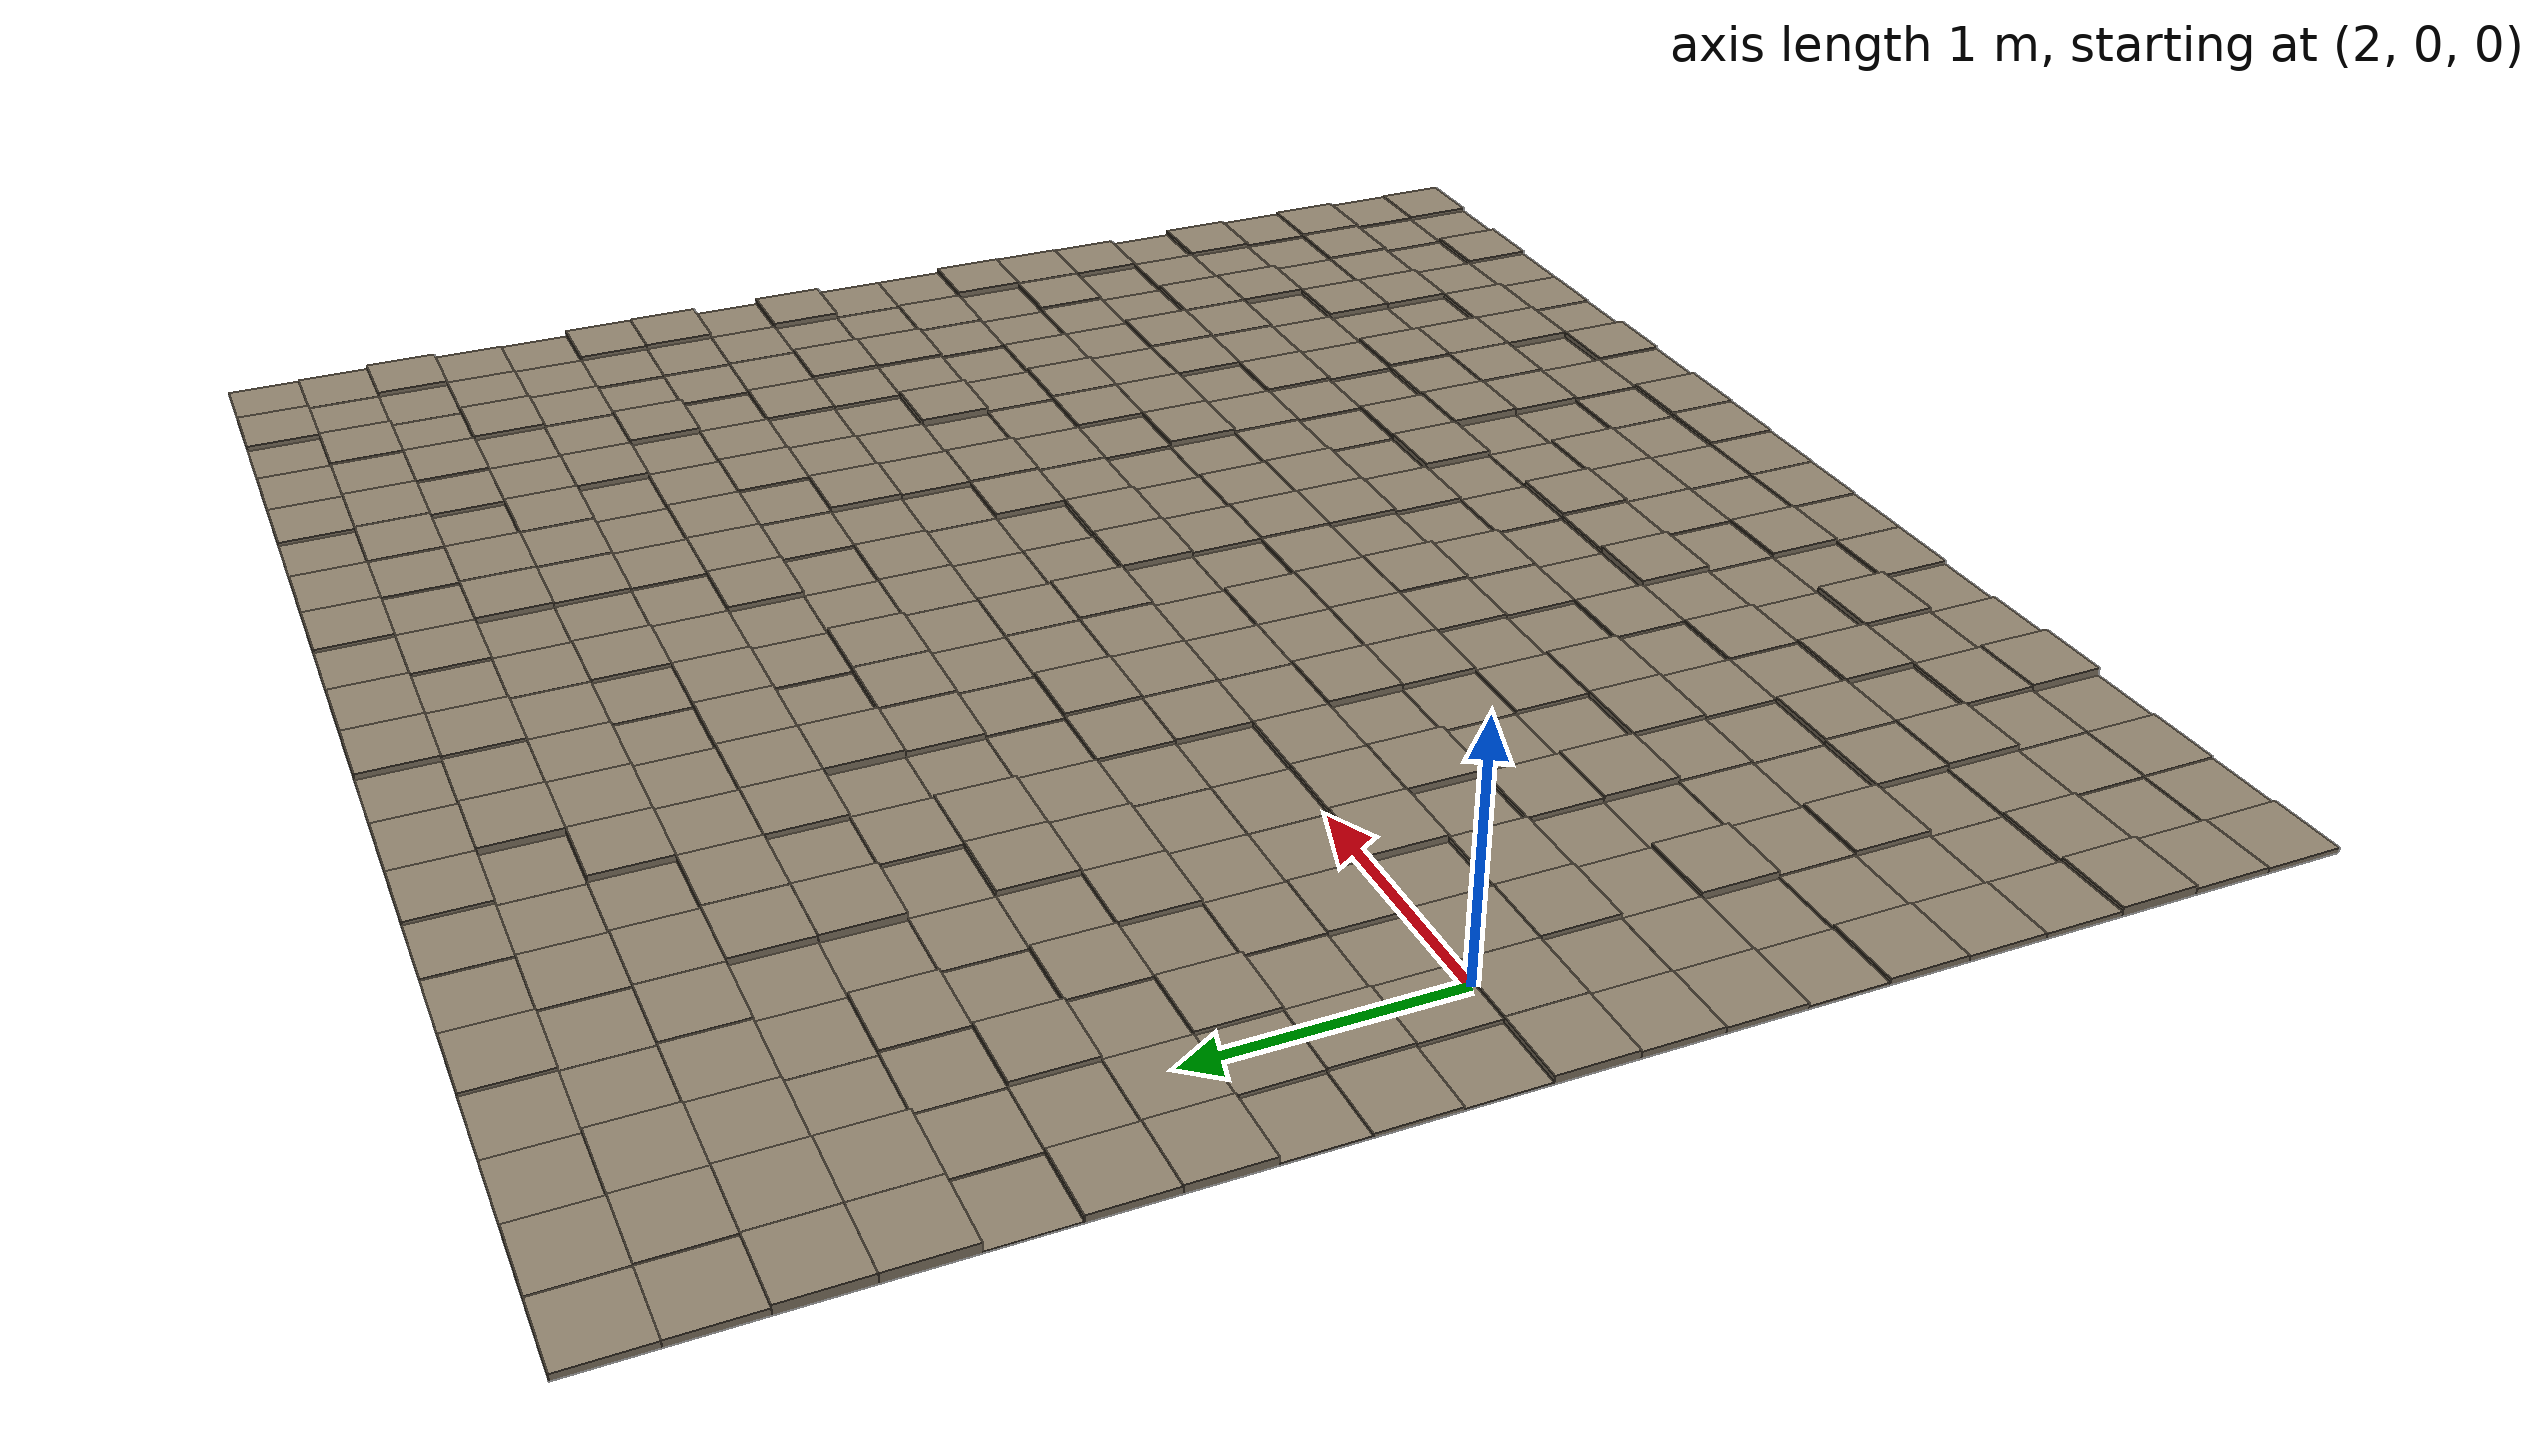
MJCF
<mujoco model="terrain rough">
  <!-- cobblestone patch, 30 cm tiles 0.5-4 cm high (scripts/make_terrain_benchmark.py) -->
  <asset>
    <material name="terrain" rgba="0.55 0.5 0.42 1"/>
  </asset>
  <worldbody>
    <geom name="tile0_0" type="box" pos="1.6500 -2.8500 0.0104" size="0.1500 0.1500 0.0104" material="terrain" contype="1" conaffinity="1" condim="3" friction="1.0 0.5 0.1"/>
    <geom name="tile0_1" type="box" pos="1.6500 -2.5500 0.0123" size="0.1500 0.1500 0.0123" material="terrain" contype="1" conaffinity="1" condim="3" friction="1.0 0.5 0.1"/>
    <geom name="tile0_2" type="box" pos="1.6500 -2.2500 0.0187" size="0.1500 0.1500 0.0187" material="terrain" contype="1" conaffinity="1" condim="3" friction="1.0 0.5 0.1"/>
    <geom name="tile0_3" type="box" pos="1.6500 -1.9500 0.0106" size="0.1500 0.1500 0.0106" material="terrain" contype="1" conaffinity="1" condim="3" friction="1.0 0.5 0.1"/>
    <geom name="tile0_4" type="box" pos="1.6500 -1.6500 0.0114" size="0.1500 0.1500 0.0114" material="terrain" contype="1" conaffinity="1" condim="3" friction="1.0 0.5 0.1"/>
    <geom name="tile0_5" type="box" pos="1.6500 -1.3500 0.0128" size="0.1500 0.1500 0.0128" material="terrain" contype="1" conaffinity="1" condim="3" friction="1.0 0.5 0.1"/>
    <geom name="tile0_6" type="box" pos="1.6500 -1.0500 0.0057" size="0.1500 0.1500 0.0057" material="terrain" contype="1" conaffinity="1" condim="3" friction="1.0 0.5 0.1"/>
    <geom name="tile0_7" type="box" pos="1.6500 -0.7500 0.0115" size="0.1500 0.1500 0.0115" material="terrain" contype="1" conaffinity="1" condim="3" friction="1.0 0.5 0.1"/>
    <geom name="tile0_8" type="box" pos="1.6500 -0.4500 0.0135" size="0.1500 0.1500 0.0135" material="terrain" contype="1" conaffinity="1" condim="3" friction="1.0 0.5 0.1"/>
    <geom name="tile0_9" type="box" pos="1.6500 -0.1500 0.0164" size="0.1500 0.1500 0.0164" material="terrain" contype="1" conaffinity="1" condim="3" friction="1.0 0.5 0.1"/>
    <geom name="tile0_10" type="box" pos="1.6500 0.1500 0.0041" size="0.1500 0.1500 0.0041" material="terrain" contype="1" conaffinity="1" condim="3" friction="1.0 0.5 0.1"/>
    <geom name="tile0_11" type="box" pos="1.6500 0.4500 0.0078" size="0.1500 0.1500 0.0078" material="terrain" contype="1" conaffinity="1" condim="3" friction="1.0 0.5 0.1"/>
    <geom name="tile0_12" type="box" pos="1.6500 0.7500 0.0041" size="0.1500 0.1500 0.0041" material="terrain" contype="1" conaffinity="1" condim="3" friction="1.0 0.5 0.1"/>
    <geom name="tile0_13" type="box" pos="1.6500 1.0500 0.0167" size="0.1500 0.1500 0.0167" material="terrain" contype="1" conaffinity="1" condim="3" friction="1.0 0.5 0.1"/>
    <geom name="tile0_14" type="box" pos="1.6500 1.3500 0.0146" size="0.1500 0.1500 0.0146" material="terrain" contype="1" conaffinity="1" condim="3" friction="1.0 0.5 0.1"/>
    <geom name="tile0_15" type="box" pos="1.6500 1.6500 0.0032" size="0.1500 0.1500 0.0032" material="terrain" contype="1" conaffinity="1" condim="3" friction="1.0 0.5 0.1"/>
    <geom name="tile0_16" type="box" pos="1.6500 1.9500 0.0197" size="0.1500 0.1500 0.0197" material="terrain" contype="1" conaffinity="1" condim="3" friction="1.0 0.5 0.1"/>
    <geom name="tile0_17" type="box" pos="1.6500 2.2500 0.0194" size="0.1500 0.1500 0.0194" material="terrain" contype="1" conaffinity="1" condim="3" friction="1.0 0.5 0.1"/>
    <geom name="tile0_18" type="box" pos="1.6500 2.5500 0.0139" size="0.1500 0.1500 0.0139" material="terrain" contype="1" conaffinity="1" condim="3" friction="1.0 0.5 0.1"/>
    <geom name="tile0_19" type="box" pos="1.6500 2.8500 0.0133" size="0.1500 0.1500 0.0133" material="terrain" contype="1" conaffinity="1" condim="3" friction="1.0 0.5 0.1"/>
    <geom name="tile1_0" type="box" pos="1.9500 -2.8500 0.0053" size="0.1500 0.1500 0.0053" material="terrain" contype="1" conaffinity="1" condim="3" friction="1.0 0.5 0.1"/>
    <geom name="tile1_1" type="box" pos="1.9500 -2.5500 0.0028" size="0.1500 0.1500 0.0028" material="terrain" contype="1" conaffinity="1" condim="3" friction="1.0 0.5 0.1"/>
    <geom name="tile1_2" type="box" pos="1.9500 -2.2500 0.0117" size="0.1500 0.1500 0.0117" material="terrain" contype="1" conaffinity="1" condim="3" friction="1.0 0.5 0.1"/>
    <geom name="tile1_3" type="box" pos="1.9500 -1.9500 0.0035" size="0.1500 0.1500 0.0035" material="terrain" contype="1" conaffinity="1" condim="3" friction="1.0 0.5 0.1"/>
    <geom name="tile1_4" type="box" pos="1.9500 -1.6500 0.0058" size="0.1500 0.1500 0.0058" material="terrain" contype="1" conaffinity="1" condim="3" friction="1.0 0.5 0.1"/>
    <geom name="tile1_5" type="box" pos="1.9500 -1.3500 0.0067" size="0.1500 0.1500 0.0067" material="terrain" contype="1" conaffinity="1" condim="3" friction="1.0 0.5 0.1"/>
    <geom name="tile1_6" type="box" pos="1.9500 -1.0500 0.0030" size="0.1500 0.1500 0.0030" material="terrain" contype="1" conaffinity="1" condim="3" friction="1.0 0.5 0.1"/>
    <geom name="tile1_7" type="box" pos="1.9500 -0.7500 0.0106" size="0.1500 0.1500 0.0106" material="terrain" contype="1" conaffinity="1" condim="3" friction="1.0 0.5 0.1"/>
    <geom name="tile1_8" type="box" pos="1.9500 -0.4500 0.0102" size="0.1500 0.1500 0.0102" material="terrain" contype="1" conaffinity="1" condim="3" friction="1.0 0.5 0.1"/>
    <geom name="tile1_9" type="box" pos="1.9500 -0.1500 0.0172" size="0.1500 0.1500 0.0172" material="terrain" contype="1" conaffinity="1" condim="3" friction="1.0 0.5 0.1"/>
    <geom name="tile1_10" type="box" pos="1.9500 0.1500 0.0116" size="0.1500 0.1500 0.0116" material="terrain" contype="1" conaffinity="1" condim="3" friction="1.0 0.5 0.1"/>
    <geom name="tile1_11" type="box" pos="1.9500 0.4500 0.0137" size="0.1500 0.1500 0.0137" material="terrain" contype="1" conaffinity="1" condim="3" friction="1.0 0.5 0.1"/>
    <geom name="tile1_12" type="box" pos="1.9500 0.7500 0.0112" size="0.1500 0.1500 0.0112" material="terrain" contype="1" conaffinity="1" condim="3" friction="1.0 0.5 0.1"/>
    <geom name="tile1_13" type="box" pos="1.9500 1.0500 0.0141" size="0.1500 0.1500 0.0141" material="terrain" contype="1" conaffinity="1" condim="3" friction="1.0 0.5 0.1"/>
    <geom name="tile1_14" type="box" pos="1.9500 1.3500 0.0105" size="0.1500 0.1500 0.0105" material="terrain" contype="1" conaffinity="1" condim="3" friction="1.0 0.5 0.1"/>
    <geom name="tile1_15" type="box" pos="1.9500 1.6500 0.0074" size="0.1500 0.1500 0.0074" material="terrain" contype="1" conaffinity="1" condim="3" friction="1.0 0.5 0.1"/>
    <geom name="tile1_16" type="box" pos="1.9500 1.9500 0.0200" size="0.1500 0.1500 0.0200" material="terrain" contype="1" conaffinity="1" condim="3" friction="1.0 0.5 0.1"/>
    <geom name="tile1_17" type="box" pos="1.9500 2.2500 0.0199" size="0.1500 0.1500 0.0199" material="terrain" contype="1" conaffinity="1" condim="3" friction="1.0 0.5 0.1"/>
    <geom name="tile1_18" type="box" pos="1.9500 2.5500 0.0172" size="0.1500 0.1500 0.0172" material="terrain" contype="1" conaffinity="1" condim="3" friction="1.0 0.5 0.1"/>
    <geom name="tile1_19" type="box" pos="1.9500 2.8500 0.0149" size="0.1500 0.1500 0.0149" material="terrain" contype="1" conaffinity="1" condim="3" friction="1.0 0.5 0.1"/>
    <geom name="tile2_0" type="box" pos="2.2500 -2.8500 0.0080" size="0.1500 0.1500 0.0080" material="terrain" contype="1" conaffinity="1" condim="3" friction="1.0 0.5 0.1"/>
    <geom name="tile2_1" type="box" pos="2.2500 -2.5500 0.0065" size="0.1500 0.1500 0.0065" material="terrain" contype="1" conaffinity="1" condim="3" friction="1.0 0.5 0.1"/>
    <geom name="tile2_2" type="box" pos="2.2500 -2.2500 0.0076" size="0.1500 0.1500 0.0076" material="terrain" contype="1" conaffinity="1" condim="3" friction="1.0 0.5 0.1"/>
    <geom name="tile2_3" type="box" pos="2.2500 -1.9500 0.0037" size="0.1500 0.1500 0.0037" material="terrain" contype="1" conaffinity="1" condim="3" friction="1.0 0.5 0.1"/>
    <geom name="tile2_4" type="box" pos="2.2500 -1.6500 0.0159" size="0.1500 0.1500 0.0159" material="terrain" contype="1" conaffinity="1" condim="3" friction="1.0 0.5 0.1"/>
    <geom name="tile2_5" type="box" pos="2.2500 -1.3500 0.0095" size="0.1500 0.1500 0.0095" material="terrain" contype="1" conaffinity="1" condim="3" friction="1.0 0.5 0.1"/>
    <geom name="tile2_6" type="box" pos="2.2500 -1.0500 0.0173" size="0.1500 0.1500 0.0173" material="terrain" contype="1" conaffinity="1" condim="3" friction="1.0 0.5 0.1"/>
    <geom name="tile2_7" type="box" pos="2.2500 -0.7500 0.0093" size="0.1500 0.1500 0.0093" material="terrain" contype="1" conaffinity="1" condim="3" friction="1.0 0.5 0.1"/>
    <geom name="tile2_8" type="box" pos="2.2500 -0.4500 0.0193" size="0.1500 0.1500 0.0193" material="terrain" contype="1" conaffinity="1" condim="3" friction="1.0 0.5 0.1"/>
    <geom name="tile2_9" type="box" pos="2.2500 -0.1500 0.0173" size="0.1500 0.1500 0.0173" material="terrain" contype="1" conaffinity="1" condim="3" friction="1.0 0.5 0.1"/>
    <geom name="tile2_10" type="box" pos="2.2500 0.1500 0.0025" size="0.1500 0.1500 0.0025" material="terrain" contype="1" conaffinity="1" condim="3" friction="1.0 0.5 0.1"/>
    <geom name="tile2_11" type="box" pos="2.2500 0.4500 0.0062" size="0.1500 0.1500 0.0062" material="terrain" contype="1" conaffinity="1" condim="3" friction="1.0 0.5 0.1"/>
    <geom name="tile2_12" type="box" pos="2.2500 0.7500 0.0184" size="0.1500 0.1500 0.0184" material="terrain" contype="1" conaffinity="1" condim="3" friction="1.0 0.5 0.1"/>
    <geom name="tile2_13" type="box" pos="2.2500 1.0500 0.0107" size="0.1500 0.1500 0.0107" material="terrain" contype="1" conaffinity="1" condim="3" friction="1.0 0.5 0.1"/>
    <geom name="tile2_14" type="box" pos="2.2500 1.3500 0.0197" size="0.1500 0.1500 0.0197" material="terrain" contype="1" conaffinity="1" condim="3" friction="1.0 0.5 0.1"/>
    <geom name="tile2_15" type="box" pos="2.2500 1.6500 0.0095" size="0.1500 0.1500 0.0095" material="terrain" contype="1" conaffinity="1" condim="3" friction="1.0 0.5 0.1"/>
    <geom name="tile2_16" type="box" pos="2.2500 1.9500 0.0038" size="0.1500 0.1500 0.0038" material="terrain" contype="1" conaffinity="1" condim="3" friction="1.0 0.5 0.1"/>
    <geom name="tile2_17" type="box" pos="2.2500 2.2500 0.0135" size="0.1500 0.1500 0.0135" material="terrain" contype="1" conaffinity="1" condim="3" friction="1.0 0.5 0.1"/>
    <geom name="tile2_18" type="box" pos="2.2500 2.5500 0.0161" size="0.1500 0.1500 0.0161" material="terrain" contype="1" conaffinity="1" condim="3" friction="1.0 0.5 0.1"/>
    <geom name="tile2_19" type="box" pos="2.2500 2.8500 0.0072" size="0.1500 0.1500 0.0072" material="terrain" contype="1" conaffinity="1" condim="3" friction="1.0 0.5 0.1"/>
    <geom name="tile3_0" type="box" pos="2.5500 -2.8500 0.0040" size="0.1500 0.1500 0.0040" material="terrain" contype="1" conaffinity="1" condim="3" friction="1.0 0.5 0.1"/>
    <geom name="tile3_1" type="box" pos="2.5500 -2.5500 0.0083" size="0.1500 0.1500 0.0083" material="terrain" contype="1" conaffinity="1" condim="3" friction="1.0 0.5 0.1"/>
    <geom name="tile3_2" type="box" pos="2.5500 -2.2500 0.0194" size="0.1500 0.1500 0.0194" material="terrain" contype="1" conaffinity="1" condim="3" friction="1.0 0.5 0.1"/>
    <geom name="tile3_3" type="box" pos="2.5500 -1.9500 0.0158" size="0.1500 0.1500 0.0158" material="terrain" contype="1" conaffinity="1" condim="3" friction="1.0 0.5 0.1"/>
    <geom name="tile3_4" type="box" pos="2.5500 -1.6500 0.0046" size="0.1500 0.1500 0.0046" material="terrain" contype="1" conaffinity="1" condim="3" friction="1.0 0.5 0.1"/>
    <geom name="tile3_5" type="box" pos="2.5500 -1.3500 0.0068" size="0.1500 0.1500 0.0068" material="terrain" contype="1" conaffinity="1" condim="3" friction="1.0 0.5 0.1"/>
    <geom name="tile3_6" type="box" pos="2.5500 -1.0500 0.0043" size="0.1500 0.1500 0.0043" material="terrain" contype="1" conaffinity="1" condim="3" friction="1.0 0.5 0.1"/>
    <geom name="tile3_7" type="box" pos="2.5500 -0.7500 0.0035" size="0.1500 0.1500 0.0035" material="terrain" contype="1" conaffinity="1" condim="3" friction="1.0 0.5 0.1"/>
    <geom name="tile3_8" type="box" pos="2.5500 -0.4500 0.0164" size="0.1500 0.1500 0.0164" material="terrain" contype="1" conaffinity="1" condim="3" friction="1.0 0.5 0.1"/>
    <geom name="tile3_9" type="box" pos="2.5500 -0.1500 0.0056" size="0.1500 0.1500 0.0056" material="terrain" contype="1" conaffinity="1" condim="3" friction="1.0 0.5 0.1"/>
    <geom name="tile3_10" type="box" pos="2.5500 0.1500 0.0123" size="0.1500 0.1500 0.0123" material="terrain" contype="1" conaffinity="1" condim="3" friction="1.0 0.5 0.1"/>
    <geom name="tile3_11" type="box" pos="2.5500 0.4500 0.0103" size="0.1500 0.1500 0.0103" material="terrain" contype="1" conaffinity="1" condim="3" friction="1.0 0.5 0.1"/>
    <geom name="tile3_12" type="box" pos="2.5500 0.7500 0.0058" size="0.1500 0.1500 0.0058" material="terrain" contype="1" conaffinity="1" condim="3" friction="1.0 0.5 0.1"/>
    <geom name="tile3_13" type="box" pos="2.5500 1.0500 0.0153" size="0.1500 0.1500 0.0153" material="terrain" contype="1" conaffinity="1" condim="3" friction="1.0 0.5 0.1"/>
    <geom name="tile3_14" type="box" pos="2.5500 1.3500 0.0048" size="0.1500 0.1500 0.0048" material="terrain" contype="1" conaffinity="1" condim="3" friction="1.0 0.5 0.1"/>
    <geom name="tile3_15" type="box" pos="2.5500 1.6500 0.0138" size="0.1500 0.1500 0.0138" material="terrain" contype="1" conaffinity="1" condim="3" friction="1.0 0.5 0.1"/>
    <geom name="tile3_16" type="box" pos="2.5500 1.9500 0.0045" size="0.1500 0.1500 0.0045" material="terrain" contype="1" conaffinity="1" condim="3" friction="1.0 0.5 0.1"/>
    <geom name="tile3_17" type="box" pos="2.5500 2.2500 0.0099" size="0.1500 0.1500 0.0099" material="terrain" contype="1" conaffinity="1" condim="3" friction="1.0 0.5 0.1"/>
    <geom name="tile3_18" type="box" pos="2.5500 2.5500 0.0062" size="0.1500 0.1500 0.0062" material="terrain" contype="1" conaffinity="1" condim="3" friction="1.0 0.5 0.1"/>
    <geom name="tile3_19" type="box" pos="2.5500 2.8500 0.0072" size="0.1500 0.1500 0.0072" material="terrain" contype="1" conaffinity="1" condim="3" friction="1.0 0.5 0.1"/>
    <geom name="tile4_0" type="box" pos="2.8500 -2.8500 0.0195" size="0.1500 0.1500 0.0195" material="terrain" contype="1" conaffinity="1" condim="3" friction="1.0 0.5 0.1"/>
    <geom name="tile4_1" type="box" pos="2.8500 -2.5500 0.0166" size="0.1500 0.1500 0.0166" material="terrain" contype="1" conaffinity="1" condim="3" friction="1.0 0.5 0.1"/>
    <geom name="tile4_2" type="box" pos="2.8500 -2.2500 0.0078" size="0.1500 0.1500 0.0078" material="terrain" contype="1" conaffinity="1" condim="3" friction="1.0 0.5 0.1"/>
    <geom name="tile4_3" type="box" pos="2.8500 -1.9500 0.0180" size="0.1500 0.1500 0.0180" material="terrain" contype="1" conaffinity="1" condim="3" friction="1.0 0.5 0.1"/>
    <geom name="tile4_4" type="box" pos="2.8500 -1.6500 0.0062" size="0.1500 0.1500 0.0062" material="terrain" contype="1" conaffinity="1" condim="3" friction="1.0 0.5 0.1"/>
    <geom name="tile4_5" type="box" pos="2.8500 -1.3500 0.0094" size="0.1500 0.1500 0.0094" material="terrain" contype="1" conaffinity="1" condim="3" friction="1.0 0.5 0.1"/>
    <geom name="tile4_6" type="box" pos="2.8500 -1.0500 0.0175" size="0.1500 0.1500 0.0175" material="terrain" contype="1" conaffinity="1" condim="3" friction="1.0 0.5 0.1"/>
    <geom name="tile4_7" type="box" pos="2.8500 -0.7500 0.0137" size="0.1500 0.1500 0.0137" material="terrain" contype="1" conaffinity="1" condim="3" friction="1.0 0.5 0.1"/>
    <geom name="tile4_8" type="box" pos="2.8500 -0.4500 0.0043" size="0.1500 0.1500 0.0043" material="terrain" contype="1" conaffinity="1" condim="3" friction="1.0 0.5 0.1"/>
    <geom name="tile4_9" type="box" pos="2.8500 -0.1500 0.0198" size="0.1500 0.1500 0.0198" material="terrain" contype="1" conaffinity="1" condim="3" friction="1.0 0.5 0.1"/>
    <geom name="tile4_10" type="box" pos="2.8500 0.1500 0.0062" size="0.1500 0.1500 0.0062" material="terrain" contype="1" conaffinity="1" condim="3" friction="1.0 0.5 0.1"/>
    <geom name="tile4_11" type="box" pos="2.8500 0.4500 0.0070" size="0.1500 0.1500 0.0070" material="terrain" contype="1" conaffinity="1" condim="3" friction="1.0 0.5 0.1"/>
    <geom name="tile4_12" type="box" pos="2.8500 0.7500 0.0160" size="0.1500 0.1500 0.0160" material="terrain" contype="1" conaffinity="1" condim="3" friction="1.0 0.5 0.1"/>
    <geom name="tile4_13" type="box" pos="2.8500 1.0500 0.0083" size="0.1500 0.1500 0.0083" material="terrain" contype="1" conaffinity="1" condim="3" friction="1.0 0.5 0.1"/>
    <geom name="tile4_14" type="box" pos="2.8500 1.3500 0.0077" size="0.1500 0.1500 0.0077" material="terrain" contype="1" conaffinity="1" condim="3" friction="1.0 0.5 0.1"/>
    <geom name="tile4_15" type="box" pos="2.8500 1.6500 0.0038" size="0.1500 0.1500 0.0038" material="terrain" contype="1" conaffinity="1" condim="3" friction="1.0 0.5 0.1"/>
    <geom name="tile4_16" type="box" pos="2.8500 1.9500 0.0041" size="0.1500 0.1500 0.0041" material="terrain" contype="1" conaffinity="1" condim="3" friction="1.0 0.5 0.1"/>
    <geom name="tile4_17" type="box" pos="2.8500 2.2500 0.0127" size="0.1500 0.1500 0.0127" material="terrain" contype="1" conaffinity="1" condim="3" friction="1.0 0.5 0.1"/>
    <geom name="tile4_18" type="box" pos="2.8500 2.5500 0.0068" size="0.1500 0.1500 0.0068" material="terrain" contype="1" conaffinity="1" condim="3" friction="1.0 0.5 0.1"/>
    <geom name="tile4_19" type="box" pos="2.8500 2.8500 0.0130" size="0.1500 0.1500 0.0130" material="terrain" contype="1" conaffinity="1" condim="3" friction="1.0 0.5 0.1"/>
    <geom name="tile5_0" type="box" pos="3.1500 -2.8500 0.0090" size="0.1500 0.1500 0.0090" material="terrain" contype="1" conaffinity="1" condim="3" friction="1.0 0.5 0.1"/>
    <geom name="tile5_1" type="box" pos="3.1500 -2.5500 0.0104" size="0.1500 0.1500 0.0104" material="terrain" contype="1" conaffinity="1" condim="3" friction="1.0 0.5 0.1"/>
    <geom name="tile5_2" type="box" pos="3.1500 -2.2500 0.0193" size="0.1500 0.1500 0.0193" material="terrain" contype="1" conaffinity="1" condim="3" friction="1.0 0.5 0.1"/>
    <geom name="tile5_3" type="box" pos="3.1500 -1.9500 0.0110" size="0.1500 0.1500 0.0110" material="terrain" contype="1" conaffinity="1" condim="3" friction="1.0 0.5 0.1"/>
    <geom name="tile5_4" type="box" pos="3.1500 -1.6500 0.0126" size="0.1500 0.1500 0.0126" material="terrain" contype="1" conaffinity="1" condim="3" friction="1.0 0.5 0.1"/>
    <geom name="tile5_5" type="box" pos="3.1500 -1.3500 0.0177" size="0.1500 0.1500 0.0177" material="terrain" contype="1" conaffinity="1" condim="3" friction="1.0 0.5 0.1"/>
    <geom name="tile5_6" type="box" pos="3.1500 -1.0500 0.0057" size="0.1500 0.1500 0.0057" material="terrain" contype="1" conaffinity="1" condim="3" friction="1.0 0.5 0.1"/>
    <geom name="tile5_7" type="box" pos="3.1500 -0.7500 0.0052" size="0.1500 0.1500 0.0052" material="terrain" contype="1" conaffinity="1" condim="3" friction="1.0 0.5 0.1"/>
    <geom name="tile5_8" type="box" pos="3.1500 -0.4500 0.0184" size="0.1500 0.1500 0.0184" material="terrain" contype="1" conaffinity="1" condim="3" friction="1.0 0.5 0.1"/>
    <geom name="tile5_9" type="box" pos="3.1500 -0.1500 0.0168" size="0.1500 0.1500 0.0168" material="terrain" contype="1" conaffinity="1" condim="3" friction="1.0 0.5 0.1"/>
    <geom name="tile5_10" type="box" pos="3.1500 0.1500 0.0069" size="0.1500 0.1500 0.0069" material="terrain" contype="1" conaffinity="1" condim="3" friction="1.0 0.5 0.1"/>
    <geom name="tile5_11" type="box" pos="3.1500 0.4500 0.0058" size="0.1500 0.1500 0.0058" material="terrain" contype="1" conaffinity="1" condim="3" friction="1.0 0.5 0.1"/>
    <geom name="tile5_12" type="box" pos="3.1500 0.7500 0.0154" size="0.1500 0.1500 0.0154" material="terrain" contype="1" conaffinity="1" condim="3" friction="1.0 0.5 0.1"/>
    <geom name="tile5_13" type="box" pos="3.1500 1.0500 0.0190" size="0.1500 0.1500 0.0190" material="terrain" contype="1" conaffinity="1" condim="3" friction="1.0 0.5 0.1"/>
    <geom name="tile5_14" type="box" pos="3.1500 1.3500 0.0059" size="0.1500 0.1500 0.0059" material="terrain" contype="1" conaffinity="1" condim="3" friction="1.0 0.5 0.1"/>
    <geom name="tile5_15" type="box" pos="3.1500 1.6500 0.0191" size="0.1500 0.1500 0.0191" material="terrain" contype="1" conaffinity="1" condim="3" friction="1.0 0.5 0.1"/>
    <geom name="tile5_16" type="box" pos="3.1500 1.9500 0.0179" size="0.1500 0.1500 0.0179" material="terrain" contype="1" conaffinity="1" condim="3" friction="1.0 0.5 0.1"/>
    <geom name="tile5_17" type="box" pos="3.1500 2.2500 0.0131" size="0.1500 0.1500 0.0131" material="terrain" contype="1" conaffinity="1" condim="3" friction="1.0 0.5 0.1"/>
    <geom name="tile5_18" type="box" pos="3.1500 2.5500 0.0099" size="0.1500 0.1500 0.0099" material="terrain" contype="1" conaffinity="1" condim="3" friction="1.0 0.5 0.1"/>
    <geom name="tile5_19" type="box" pos="3.1500 2.8500 0.0043" size="0.1500 0.1500 0.0043" material="terrain" contype="1" conaffinity="1" condim="3" friction="1.0 0.5 0.1"/>
    <geom name="tile6_0" type="box" pos="3.4500 -2.8500 0.0032" size="0.1500 0.1500 0.0032" material="terrain" contype="1" conaffinity="1" condim="3" friction="1.0 0.5 0.1"/>
    <geom name="tile6_1" type="box" pos="3.4500 -2.5500 0.0193" size="0.1500 0.1500 0.0193" material="terrain" contype="1" conaffinity="1" condim="3" friction="1.0 0.5 0.1"/>
    <geom name="tile6_2" type="box" pos="3.4500 -2.2500 0.0067" size="0.1500 0.1500 0.0067" material="terrain" contype="1" conaffinity="1" condim="3" friction="1.0 0.5 0.1"/>
    <geom name="tile6_3" type="box" pos="3.4500 -1.9500 0.0148" size="0.1500 0.1500 0.0148" material="terrain" contype="1" conaffinity="1" condim="3" friction="1.0 0.5 0.1"/>
    <geom name="tile6_4" type="box" pos="3.4500 -1.6500 0.0070" size="0.1500 0.1500 0.0070" material="terrain" contype="1" conaffinity="1" condim="3" friction="1.0 0.5 0.1"/>
    <geom name="tile6_5" type="box" pos="3.4500 -1.3500 0.0169" size="0.1500 0.1500 0.0169" material="terrain" contype="1" conaffinity="1" condim="3" friction="1.0 0.5 0.1"/>
    <geom name="tile6_6" type="box" pos="3.4500 -1.0500 0.0129" size="0.1500 0.1500 0.0129" material="terrain" contype="1" conaffinity="1" condim="3" friction="1.0 0.5 0.1"/>
    <geom name="tile6_7" type="box" pos="3.4500 -0.7500 0.0076" size="0.1500 0.1500 0.0076" material="terrain" contype="1" conaffinity="1" condim="3" friction="1.0 0.5 0.1"/>
    <geom name="tile6_8" type="box" pos="3.4500 -0.4500 0.0056" size="0.1500 0.1500 0.0056" material="terrain" contype="1" conaffinity="1" condim="3" friction="1.0 0.5 0.1"/>
    <geom name="tile6_9" type="box" pos="3.4500 -0.1500 0.0151" size="0.1500 0.1500 0.0151" material="terrain" contype="1" conaffinity="1" condim="3" friction="1.0 0.5 0.1"/>
    <geom name="tile6_10" type="box" pos="3.4500 0.1500 0.0037" size="0.1500 0.1500 0.0037" material="terrain" contype="1" conaffinity="1" condim="3" friction="1.0 0.5 0.1"/>
    <geom name="tile6_11" type="box" pos="3.4500 0.4500 0.0065" size="0.1500 0.1500 0.0065" material="terrain" contype="1" conaffinity="1" condim="3" friction="1.0 0.5 0.1"/>
    <geom name="tile6_12" type="box" pos="3.4500 0.7500 0.0123" size="0.1500 0.1500 0.0123" material="terrain" contype="1" conaffinity="1" condim="3" friction="1.0 0.5 0.1"/>
    <geom name="tile6_13" type="box" pos="3.4500 1.0500 0.0174" size="0.1500 0.1500 0.0174" material="terrain" contype="1" conaffinity="1" condim="3" friction="1.0 0.5 0.1"/>
    <geom name="tile6_14" type="box" pos="3.4500 1.3500 0.0133" size="0.1500 0.1500 0.0133" material="terrain" contype="1" conaffinity="1" condim="3" friction="1.0 0.5 0.1"/>
    <geom name="tile6_15" type="box" pos="3.4500 1.6500 0.0074" size="0.1500 0.1500 0.0074" material="terrain" contype="1" conaffinity="1" condim="3" friction="1.0 0.5 0.1"/>
    <geom name="tile6_16" type="box" pos="3.4500 1.9500 0.0186" size="0.1500 0.1500 0.0186" material="terrain" contype="1" conaffinity="1" condim="3" friction="1.0 0.5 0.1"/>
    <geom name="tile6_17" type="box" pos="3.4500 2.2500 0.0061" size="0.1500 0.1500 0.0061" material="terrain" contype="1" conaffinity="1" condim="3" friction="1.0 0.5 0.1"/>
    <geom name="tile6_18" type="box" pos="3.4500 2.5500 0.0028" size="0.1500 0.1500 0.0028" material="terrain" contype="1" conaffinity="1" condim="3" friction="1.0 0.5 0.1"/>
    <geom name="tile6_19" type="box" pos="3.4500 2.8500 0.0072" size="0.1500 0.1500 0.0072" material="terrain" contype="1" conaffinity="1" condim="3" friction="1.0 0.5 0.1"/>
    <geom name="tile7_0" type="box" pos="3.7500 -2.8500 0.0103" size="0.1500 0.1500 0.0103" material="terrain" contype="1" conaffinity="1" condim="3" friction="1.0 0.5 0.1"/>
    <geom name="tile7_1" type="box" pos="3.7500 -2.5500 0.0036" size="0.1500 0.1500 0.0036" material="terrain" contype="1" conaffinity="1" condim="3" friction="1.0 0.5 0.1"/>
    <geom name="tile7_2" type="box" pos="3.7500 -2.2500 0.0056" size="0.1500 0.1500 0.0056" material="terrain" contype="1" conaffinity="1" condim="3" friction="1.0 0.5 0.1"/>
    <geom name="tile7_3" type="box" pos="3.7500 -1.9500 0.0090" size="0.1500 0.1500 0.0090" material="terrain" contype="1" conaffinity="1" condim="3" friction="1.0 0.5 0.1"/>
    <geom name="tile7_4" type="box" pos="3.7500 -1.6500 0.0125" size="0.1500 0.1500 0.0125" material="terrain" contype="1" conaffinity="1" condim="3" friction="1.0 0.5 0.1"/>
    <geom name="tile7_5" type="box" pos="3.7500 -1.3500 0.0048" size="0.1500 0.1500 0.0048" material="terrain" contype="1" conaffinity="1" condim="3" friction="1.0 0.5 0.1"/>
    <geom name="tile7_6" type="box" pos="3.7500 -1.0500 0.0088" size="0.1500 0.1500 0.0088" material="terrain" contype="1" conaffinity="1" condim="3" friction="1.0 0.5 0.1"/>
    <geom name="tile7_7" type="box" pos="3.7500 -0.7500 0.0181" size="0.1500 0.1500 0.0181" material="terrain" contype="1" conaffinity="1" condim="3" friction="1.0 0.5 0.1"/>
    <geom name="tile7_8" type="box" pos="3.7500 -0.4500 0.0197" size="0.1500 0.1500 0.0197" material="terrain" contype="1" conaffinity="1" condim="3" friction="1.0 0.5 0.1"/>
    <geom name="tile7_9" type="box" pos="3.7500 -0.1500 0.0140" size="0.1500 0.1500 0.0140" material="terrain" contype="1" conaffinity="1" condim="3" friction="1.0 0.5 0.1"/>
    <geom name="tile7_10" type="box" pos="3.7500 0.1500 0.0146" size="0.1500 0.1500 0.0146" material="terrain" contype="1" conaffinity="1" condim="3" friction="1.0 0.5 0.1"/>
    <geom name="tile7_11" type="box" pos="3.7500 0.4500 0.0127" size="0.1500 0.1500 0.0127" material="terrain" contype="1" conaffinity="1" condim="3" friction="1.0 0.5 0.1"/>
    <geom name="tile7_12" type="box" pos="3.7500 0.7500 0.0050" size="0.1500 0.1500 0.0050" material="terrain" contype="1" conaffinity="1" condim="3" friction="1.0 0.5 0.1"/>
    <geom name="tile7_13" type="box" pos="3.7500 1.0500 0.0031" size="0.1500 0.1500 0.0031" material="terrain" contype="1" conaffinity="1" condim="3" friction="1.0 0.5 0.1"/>
    <geom name="tile7_14" type="box" pos="3.7500 1.3500 0.0028" size="0.1500 0.1500 0.0028" material="terrain" contype="1" conaffinity="1" condim="3" friction="1.0 0.5 0.1"/>
    <geom name="tile7_15" type="box" pos="3.7500 1.6500 0.0184" size="0.1500 0.1500 0.0184" material="terrain" contype="1" conaffinity="1" condim="3" friction="1.0 0.5 0.1"/>
    <geom name="tile7_16" type="box" pos="3.7500 1.9500 0.0148" size="0.1500 0.1500 0.0148" material="terrain" contype="1" conaffinity="1" condim="3" friction="1.0 0.5 0.1"/>
    <geom name="tile7_17" type="box" pos="3.7500 2.2500 0.0193" size="0.1500 0.1500 0.0193" material="terrain" contype="1" conaffinity="1" condim="3" friction="1.0 0.5 0.1"/>
    <geom name="tile7_18" type="box" pos="3.7500 2.5500 0.0029" size="0.1500 0.1500 0.0029" material="terrain" contype="1" conaffinity="1" condim="3" friction="1.0 0.5 0.1"/>
    <geom name="tile7_19" type="box" pos="3.7500 2.8500 0.0136" size="0.1500 0.1500 0.0136" material="terrain" contype="1" conaffinity="1" condim="3" friction="1.0 0.5 0.1"/>
    <geom name="tile8_0" type="box" pos="4.0500 -2.8500 0.0109" size="0.1500 0.1500 0.0109" material="terrain" contype="1" conaffinity="1" condim="3" friction="1.0 0.5 0.1"/>
    <geom name="tile8_1" type="box" pos="4.0500 -2.5500 0.0153" size="0.1500 0.1500 0.0153" material="terrain" contype="1" conaffinity="1" condim="3" friction="1.0 0.5 0.1"/>
    <geom name="tile8_2" type="box" pos="4.0500 -2.2500 0.0081" size="0.1500 0.1500 0.0081" material="terrain" contype="1" conaffinity="1" condim="3" friction="1.0 0.5 0.1"/>
    <geom name="tile8_3" type="box" pos="4.0500 -1.9500 0.0200" size="0.1500 0.1500 0.0200" material="terrain" contype="1" conaffinity="1" condim="3" friction="1.0 0.5 0.1"/>
    <geom name="tile8_4" type="box" pos="4.0500 -1.6500 0.0038" size="0.1500 0.1500 0.0038" material="terrain" contype="1" conaffinity="1" condim="3" friction="1.0 0.5 0.1"/>
    <geom name="tile8_5" type="box" pos="4.0500 -1.3500 0.0121" size="0.1500 0.1500 0.0121" material="terrain" contype="1" conaffinity="1" condim="3" friction="1.0 0.5 0.1"/>
    <geom name="tile8_6" type="box" pos="4.0500 -1.0500 0.0154" size="0.1500 0.1500 0.0154" material="terrain" contype="1" conaffinity="1" condim="3" friction="1.0 0.5 0.1"/>
    <geom name="tile8_7" type="box" pos="4.0500 -0.7500 0.0183" size="0.1500 0.1500 0.0183" material="terrain" contype="1" conaffinity="1" condim="3" friction="1.0 0.5 0.1"/>
    <geom name="tile8_8" type="box" pos="4.0500 -0.4500 0.0154" size="0.1500 0.1500 0.0154" material="terrain" contype="1" conaffinity="1" condim="3" friction="1.0 0.5 0.1"/>
    <geom name="tile8_9" type="box" pos="4.0500 -0.1500 0.0148" size="0.1500 0.1500 0.0148" material="terrain" contype="1" conaffinity="1" condim="3" friction="1.0 0.5 0.1"/>
    <geom name="tile8_10" type="box" pos="4.0500 0.1500 0.0164" size="0.1500 0.1500 0.0164" material="terrain" contype="1" conaffinity="1" condim="3" friction="1.0 0.5 0.1"/>
    <geom name="tile8_11" type="box" pos="4.0500 0.4500 0.0185" size="0.1500 0.1500 0.0185" material="terrain" contype="1" conaffinity="1" condim="3" friction="1.0 0.5 0.1"/>
    <geom name="tile8_12" type="box" pos="4.0500 0.7500 0.0087" size="0.1500 0.1500 0.0087" material="terrain" contype="1" conaffinity="1" condim="3" friction="1.0 0.5 0.1"/>
    <geom name="tile8_13" type="box" pos="4.0500 1.0500 0.0145" size="0.1500 0.1500 0.0145" material="terrain" contype="1" conaffinity="1" condim="3" friction="1.0 0.5 0.1"/>
    <geom name="tile8_14" type="box" pos="4.0500 1.3500 0.0183" size="0.1500 0.1500 0.0183" material="terrain" contype="1" conaffinity="1" condim="3" friction="1.0 0.5 0.1"/>
    <geom name="tile8_15" type="box" pos="4.0500 1.6500 0.0177" size="0.1500 0.1500 0.0177" material="terrain" contype="1" conaffinity="1" condim="3" friction="1.0 0.5 0.1"/>
    <geom name="tile8_16" type="box" pos="4.0500 1.9500 0.0098" size="0.1500 0.1500 0.0098" material="terrain" contype="1" conaffinity="1" condim="3" friction="1.0 0.5 0.1"/>
    <geom name="tile8_17" type="box" pos="4.0500 2.2500 0.0163" size="0.1500 0.1500 0.0163" material="terrain" contype="1" conaffinity="1" condim="3" friction="1.0 0.5 0.1"/>
    <geom name="tile8_18" type="box" pos="4.0500 2.5500 0.0176" size="0.1500 0.1500 0.0176" material="terrain" contype="1" conaffinity="1" condim="3" friction="1.0 0.5 0.1"/>
    <geom name="tile8_19" type="box" pos="4.0500 2.8500 0.0125" size="0.1500 0.1500 0.0125" material="terrain" contype="1" conaffinity="1" condim="3" friction="1.0 0.5 0.1"/>
    <geom name="tile9_0" type="box" pos="4.3500 -2.8500 0.0134" size="0.1500 0.1500 0.0134" material="terrain" contype="1" conaffinity="1" condim="3" friction="1.0 0.5 0.1"/>
    <geom name="tile9_1" type="box" pos="4.3500 -2.5500 0.0092" size="0.1500 0.1500 0.0092" material="terrain" contype="1" conaffinity="1" condim="3" friction="1.0 0.5 0.1"/>
    <geom name="tile9_2" type="box" pos="4.3500 -2.2500 0.0127" size="0.1500 0.1500 0.0127" material="terrain" contype="1" conaffinity="1" condim="3" friction="1.0 0.5 0.1"/>
    <geom name="tile9_3" type="box" pos="4.3500 -1.9500 0.0132" size="0.1500 0.1500 0.0132" material="terrain" contype="1" conaffinity="1" condim="3" friction="1.0 0.5 0.1"/>
    <geom name="tile9_4" type="box" pos="4.3500 -1.6500 0.0039" size="0.1500 0.1500 0.0039" material="terrain" contype="1" conaffinity="1" condim="3" friction="1.0 0.5 0.1"/>
    <geom name="tile9_5" type="box" pos="4.3500 -1.3500 0.0137" size="0.1500 0.1500 0.0137" material="terrain" contype="1" conaffinity="1" condim="3" friction="1.0 0.5 0.1"/>
    <geom name="tile9_6" type="box" pos="4.3500 -1.0500 0.0199" size="0.1500 0.1500 0.0199" material="terrain" contype="1" conaffinity="1" condim="3" friction="1.0 0.5 0.1"/>
    <geom name="tile9_7" type="box" pos="4.3500 -0.7500 0.0179" size="0.1500 0.1500 0.0179" material="terrain" contype="1" conaffinity="1" condim="3" friction="1.0 0.5 0.1"/>
    <geom name="tile9_8" type="box" pos="4.3500 -0.4500 0.0152" size="0.1500 0.1500 0.0152" material="terrain" contype="1" conaffinity="1" condim="3" friction="1.0 0.5 0.1"/>
    <geom name="tile9_9" type="box" pos="4.3500 -0.1500 0.0093" size="0.1500 0.1500 0.0093" material="terrain" contype="1" conaffinity="1" condim="3" friction="1.0 0.5 0.1"/>
    <geom name="tile9_10" type="box" pos="4.3500 0.1500 0.0154" size="0.1500 0.1500 0.0154" material="terrain" contype="1" conaffinity="1" condim="3" friction="1.0 0.5 0.1"/>
    <geom name="tile9_11" type="box" pos="4.3500 0.4500 0.0127" size="0.1500 0.1500 0.0127" material="terrain" contype="1" conaffinity="1" condim="3" friction="1.0 0.5 0.1"/>
    <geom name="tile9_12" type="box" pos="4.3500 0.7500 0.0102" size="0.1500 0.1500 0.0102" material="terrain" contype="1" conaffinity="1" condim="3" friction="1.0 0.5 0.1"/>
    <geom name="tile9_13" type="box" pos="4.3500 1.0500 0.0172" size="0.1500 0.1500 0.0172" material="terrain" contype="1" conaffinity="1" condim="3" friction="1.0 0.5 0.1"/>
    <geom name="tile9_14" type="box" pos="4.3500 1.3500 0.0040" size="0.1500 0.1500 0.0040" material="terrain" contype="1" conaffinity="1" condim="3" friction="1.0 0.5 0.1"/>
    <geom name="tile9_15" type="box" pos="4.3500 1.6500 0.0156" size="0.1500 0.1500 0.0156" material="terrain" contype="1" conaffinity="1" condim="3" friction="1.0 0.5 0.1"/>
    <geom name="tile9_16" type="box" pos="4.3500 1.9500 0.0030" size="0.1500 0.1500 0.0030" material="terrain" contype="1" conaffinity="1" condim="3" friction="1.0 0.5 0.1"/>
    <geom name="tile9_17" type="box" pos="4.3500 2.2500 0.0130" size="0.1500 0.1500 0.0130" material="terrain" contype="1" conaffinity="1" condim="3" friction="1.0 0.5 0.1"/>
    <geom name="tile9_18" type="box" pos="4.3500 2.5500 0.0109" size="0.1500 0.1500 0.0109" material="terrain" contype="1" conaffinity="1" condim="3" friction="1.0 0.5 0.1"/>
    <geom name="tile9_19" type="box" pos="4.3500 2.8500 0.0065" size="0.1500 0.1500 0.0065" material="terrain" contype="1" conaffinity="1" condim="3" friction="1.0 0.5 0.1"/>
    <geom name="tile10_0" type="box" pos="4.6500 -2.8500 0.0147" size="0.1500 0.1500 0.0147" material="terrain" contype="1" conaffinity="1" condim="3" friction="1.0 0.5 0.1"/>
    <geom name="tile10_1" type="box" pos="4.6500 -2.5500 0.0112" size="0.1500 0.1500 0.0112" material="terrain" contype="1" conaffinity="1" condim="3" friction="1.0 0.5 0.1"/>
    <geom name="tile10_2" type="box" pos="4.6500 -2.2500 0.0133" size="0.1500 0.1500 0.0133" material="terrain" contype="1" conaffinity="1" condim="3" friction="1.0 0.5 0.1"/>
    <geom name="tile10_3" type="box" pos="4.6500 -1.9500 0.0186" size="0.1500 0.1500 0.0186" material="terrain" contype="1" conaffinity="1" condim="3" friction="1.0 0.5 0.1"/>
    <geom name="tile10_4" type="box" pos="4.6500 -1.6500 0.0070" size="0.1500 0.1500 0.0070" material="terrain" contype="1" conaffinity="1" condim="3" friction="1.0 0.5 0.1"/>
    <geom name="tile10_5" type="box" pos="4.6500 -1.3500 0.0027" size="0.1500 0.1500 0.0027" material="terrain" contype="1" conaffinity="1" condim="3" friction="1.0 0.5 0.1"/>
    <geom name="tile10_6" type="box" pos="4.6500 -1.0500 0.0078" size="0.1500 0.1500 0.0078" material="terrain" contype="1" conaffinity="1" condim="3" friction="1.0 0.5 0.1"/>
    <geom name="tile10_7" type="box" pos="4.6500 -0.7500 0.0144" size="0.1500 0.1500 0.0144" material="terrain" contype="1" conaffinity="1" condim="3" friction="1.0 0.5 0.1"/>
    <geom name="tile10_8" type="box" pos="4.6500 -0.4500 0.0060" size="0.1500 0.1500 0.0060" material="terrain" contype="1" conaffinity="1" condim="3" friction="1.0 0.5 0.1"/>
    <geom name="tile10_9" type="box" pos="4.6500 -0.1500 0.0055" size="0.1500 0.1500 0.0055" material="terrain" contype="1" conaffinity="1" condim="3" friction="1.0 0.5 0.1"/>
    <geom name="tile10_10" type="box" pos="4.6500 0.1500 0.0184" size="0.1500 0.1500 0.0184" material="terrain" contype="1" conaffinity="1" condim="3" friction="1.0 0.5 0.1"/>
    <geom name="tile10_11" type="box" pos="4.6500 0.4500 0.0140" size="0.1500 0.1500 0.0140" material="terrain" contype="1" conaffinity="1" condim="3" friction="1.0 0.5 0.1"/>
    <geom name="tile10_12" type="box" pos="4.6500 0.7500 0.0102" size="0.1500 0.1500 0.0102" material="terrain" contype="1" conaffinity="1" condim="3" friction="1.0 0.5 0.1"/>
    <geom name="tile10_13" type="box" pos="4.6500 1.0500 0.0181" size="0.1500 0.1500 0.0181" material="terrain" contype="1" conaffinity="1" condim="3" friction="1.0 0.5 0.1"/>
    <geom name="tile10_14" type="box" pos="4.6500 1.3500 0.0082" size="0.1500 0.1500 0.0082" material="terrain" contype="1" conaffinity="1" condim="3" friction="1.0 0.5 0.1"/>
    <geom name="tile10_15" type="box" pos="4.6500 1.6500 0.0142" size="0.1500 0.1500 0.0142" material="terrain" contype="1" conaffinity="1" condim="3" friction="1.0 0.5 0.1"/>
    <geom name="tile10_16" type="box" pos="4.6500 1.9500 0.0060" size="0.1500 0.1500 0.0060" material="terrain" contype="1" conaffinity="1" condim="3" friction="1.0 0.5 0.1"/>
    <geom name="tile10_17" type="box" pos="4.6500 2.2500 0.0100" size="0.1500 0.1500 0.0100" material="terrain" contype="1" conaffinity="1" condim="3" friction="1.0 0.5 0.1"/>
    <geom name="tile10_18" type="box" pos="4.6500 2.5500 0.0166" size="0.1500 0.1500 0.0166" material="terrain" contype="1" conaffinity="1" condim="3" friction="1.0 0.5 0.1"/>
    <geom name="tile10_19" type="box" pos="4.6500 2.8500 0.0185" size="0.1500 0.1500 0.0185" material="terrain" contype="1" conaffinity="1" condim="3" friction="1.0 0.5 0.1"/>
    <geom name="tile11_0" type="box" pos="4.9500 -2.8500 0.0179" size="0.1500 0.1500 0.0179" material="terrain" contype="1" conaffinity="1" condim="3" friction="1.0 0.5 0.1"/>
    <geom name="tile11_1" type="box" pos="4.9500 -2.5500 0.0092" size="0.1500 0.1500 0.0092" material="terrain" contype="1" conaffinity="1" condim="3" friction="1.0 0.5 0.1"/>
    <geom name="tile11_2" type="box" pos="4.9500 -2.2500 0.0127" size="0.1500 0.1500 0.0127" material="terrain" contype="1" conaffinity="1" condim="3" friction="1.0 0.5 0.1"/>
    <geom name="tile11_3" type="box" pos="4.9500 -1.9500 0.0080" size="0.1500 0.1500 0.0080" material="terrain" contype="1" conaffinity="1" condim="3" friction="1.0 0.5 0.1"/>
    <geom name="tile11_4" type="box" pos="4.9500 -1.6500 0.0049" size="0.1500 0.1500 0.0049" material="terrain" contype="1" conaffinity="1" condim="3" friction="1.0 0.5 0.1"/>
    <geom name="tile11_5" type="box" pos="4.9500 -1.3500 0.0112" size="0.1500 0.1500 0.0112" material="terrain" contype="1" conaffinity="1" condim="3" friction="1.0 0.5 0.1"/>
    <geom name="tile11_6" type="box" pos="4.9500 -1.0500 0.0171" size="0.1500 0.1500 0.0171" material="terrain" contype="1" conaffinity="1" condim="3" friction="1.0 0.5 0.1"/>
    <geom name="tile11_7" type="box" pos="4.9500 -0.7500 0.0174" size="0.1500 0.1500 0.0174" material="terrain" contype="1" conaffinity="1" condim="3" friction="1.0 0.5 0.1"/>
    <geom name="tile11_8" type="box" pos="4.9500 -0.4500 0.0149" size="0.1500 0.1500 0.0149" material="terrain" contype="1" conaffinity="1" condim="3" friction="1.0 0.5 0.1"/>
    <geom name="tile11_9" type="box" pos="4.9500 -0.1500 0.0191" size="0.1500 0.1500 0.0191" material="terrain" contype="1" conaffinity="1" condim="3" friction="1.0 0.5 0.1"/>
    <geom name="tile11_10" type="box" pos="4.9500 0.1500 0.0073" size="0.1500 0.1500 0.0073" material="terrain" contype="1" conaffinity="1" condim="3" friction="1.0 0.5 0.1"/>
    <geom name="tile11_11" type="box" pos="4.9500 0.4500 0.0055" size="0.1500 0.1500 0.0055" material="terrain" contype="1" conaffinity="1" condim="3" friction="1.0 0.5 0.1"/>
    <geom name="tile11_12" type="box" pos="4.9500 0.7500 0.0104" size="0.1500 0.1500 0.0104" material="terrain" contype="1" conaffinity="1" condim="3" friction="1.0 0.5 0.1"/>
    <geom name="tile11_13" type="box" pos="4.9500 1.0500 0.0073" size="0.1500 0.1500 0.0073" material="terrain" contype="1" conaffinity="1" condim="3" friction="1.0 0.5 0.1"/>
    <geom name="tile11_14" type="box" pos="4.9500 1.3500 0.0062" size="0.1500 0.1500 0.0062" material="terrain" contype="1" conaffinity="1" condim="3" friction="1.0 0.5 0.1"/>
    <geom name="tile11_15" type="box" pos="4.9500 1.6500 0.0097" size="0.1500 0.1500 0.0097" material="terrain" contype="1" conaffinity="1" condim="3" friction="1.0 0.5 0.1"/>
    <geom name="tile11_16" type="box" pos="4.9500 1.9500 0.0135" size="0.1500 0.1500 0.0135" material="terrain" contype="1" conaffinity="1" condim="3" friction="1.0 0.5 0.1"/>
    <geom name="tile11_17" type="box" pos="4.9500 2.2500 0.0111" size="0.1500 0.1500 0.0111" material="terrain" contype="1" conaffinity="1" condim="3" friction="1.0 0.5 0.1"/>
    <geom name="tile11_18" type="box" pos="4.9500 2.5500 0.0080" size="0.1500 0.1500 0.0080" material="terrain" contype="1" conaffinity="1" condim="3" friction="1.0 0.5 0.1"/>
    <geom name="tile11_19" type="box" pos="4.9500 2.8500 0.0172" size="0.1500 0.1500 0.0172" material="terrain" contype="1" conaffinity="1" condim="3" friction="1.0 0.5 0.1"/>
    <geom name="tile12_0" type="box" pos="5.2500 -2.8500 0.0197" size="0.1500 0.1500 0.0197" material="terrain" contype="1" conaffinity="1" condim="3" friction="1.0 0.5 0.1"/>
    <geom name="tile12_1" type="box" pos="5.2500 -2.5500 0.0104" size="0.1500 0.1500 0.0104" material="terrain" contype="1" conaffinity="1" condim="3" friction="1.0 0.5 0.1"/>
    <geom name="tile12_2" type="box" pos="5.2500 -2.2500 0.0038" size="0.1500 0.1500 0.0038" material="terrain" contype="1" conaffinity="1" condim="3" friction="1.0 0.5 0.1"/>
    <geom name="tile12_3" type="box" pos="5.2500 -1.9500 0.0031" size="0.1500 0.1500 0.0031" material="terrain" contype="1" conaffinity="1" condim="3" friction="1.0 0.5 0.1"/>
    <geom name="tile12_4" type="box" pos="5.2500 -1.6500 0.0178" size="0.1500 0.1500 0.0178" material="terrain" contype="1" conaffinity="1" condim="3" friction="1.0 0.5 0.1"/>
    <geom name="tile12_5" type="box" pos="5.2500 -1.3500 0.0032" size="0.1500 0.1500 0.0032" material="terrain" contype="1" conaffinity="1" condim="3" friction="1.0 0.5 0.1"/>
    <geom name="tile12_6" type="box" pos="5.2500 -1.0500 0.0149" size="0.1500 0.1500 0.0149" material="terrain" contype="1" conaffinity="1" condim="3" friction="1.0 0.5 0.1"/>
    <geom name="tile12_7" type="box" pos="5.2500 -0.7500 0.0125" size="0.1500 0.1500 0.0125" material="terrain" contype="1" conaffinity="1" condim="3" friction="1.0 0.5 0.1"/>
    <geom name="tile12_8" type="box" pos="5.2500 -0.4500 0.0079" size="0.1500 0.1500 0.0079" material="terrain" contype="1" conaffinity="1" condim="3" friction="1.0 0.5 0.1"/>
    <geom name="tile12_9" type="box" pos="5.2500 -0.1500 0.0164" size="0.1500 0.1500 0.0164" material="terrain" contype="1" conaffinity="1" condim="3" friction="1.0 0.5 0.1"/>
    <geom name="tile12_10" type="box" pos="5.2500 0.1500 0.0028" size="0.1500 0.1500 0.0028" material="terrain" contype="1" conaffinity="1" condim="3" friction="1.0 0.5 0.1"/>
    <geom name="tile12_11" type="box" pos="5.2500 0.4500 0.0049" size="0.1500 0.1500 0.0049" material="terrain" contype="1" conaffinity="1" condim="3" friction="1.0 0.5 0.1"/>
    <geom name="tile12_12" type="box" pos="5.2500 0.7500 0.0105" size="0.1500 0.1500 0.0105" material="terrain" contype="1" conaffinity="1" condim="3" friction="1.0 0.5 0.1"/>
    <geom name="tile12_13" type="box" pos="5.2500 1.0500 0.0029" size="0.1500 0.1500 0.0029" material="terrain" contype="1" conaffinity="1" condim="3" friction="1.0 0.5 0.1"/>
    <geom name="tile12_14" type="box" pos="5.2500 1.3500 0.0170" size="0.1500 0.1500 0.0170" material="terrain" contype="1" conaffinity="1" condim="3" friction="1.0 0.5 0.1"/>
    <geom name="tile12_15" type="box" pos="5.2500 1.6500 0.0067" size="0.1500 0.1500 0.0067" material="terrain" contype="1" conaffinity="1" condim="3" friction="1.0 0.5 0.1"/>
    <geom name="tile12_16" type="box" pos="5.2500 1.9500 0.0050" size="0.1500 0.1500 0.0050" material="terrain" contype="1" conaffinity="1" condim="3" friction="1.0 0.5 0.1"/>
    <geom name="tile12_17" type="box" pos="5.2500 2.2500 0.0033" size="0.1500 0.1500 0.0033" material="terrain" contype="1" conaffinity="1" condim="3" friction="1.0 0.5 0.1"/>
    <geom name="tile12_18" type="box" pos="5.2500 2.5500 0.0135" size="0.1500 0.1500 0.0135" material="terrain" contype="1" conaffinity="1" condim="3" friction="1.0 0.5 0.1"/>
    <geom name="tile12_19" type="box" pos="5.2500 2.8500 0.0103" size="0.1500 0.1500 0.0103" material="terrain" contype="1" conaffinity="1" condim="3" friction="1.0 0.5 0.1"/>
    <geom name="tile13_0" type="box" pos="5.5500 -2.8500 0.0135" size="0.1500 0.1500 0.0135" material="terrain" contype="1" conaffinity="1" condim="3" friction="1.0 0.5 0.1"/>
    <geom name="tile13_1" type="box" pos="5.5500 -2.5500 0.0140" size="0.1500 0.1500 0.0140" material="terrain" contype="1" conaffinity="1" condim="3" friction="1.0 0.5 0.1"/>
    <geom name="tile13_2" type="box" pos="5.5500 -2.2500 0.0166" size="0.1500 0.1500 0.0166" material="terrain" contype="1" conaffinity="1" condim="3" friction="1.0 0.5 0.1"/>
    <geom name="tile13_3" type="box" pos="5.5500 -1.9500 0.0193" size="0.1500 0.1500 0.0193" material="terrain" contype="1" conaffinity="1" condim="3" friction="1.0 0.5 0.1"/>
    <geom name="tile13_4" type="box" pos="5.5500 -1.6500 0.0145" size="0.1500 0.1500 0.0145" material="terrain" contype="1" conaffinity="1" condim="3" friction="1.0 0.5 0.1"/>
    <geom name="tile13_5" type="box" pos="5.5500 -1.3500 0.0060" size="0.1500 0.1500 0.0060" material="terrain" contype="1" conaffinity="1" condim="3" friction="1.0 0.5 0.1"/>
    <geom name="tile13_6" type="box" pos="5.5500 -1.0500 0.0108" size="0.1500 0.1500 0.0108" material="terrain" contype="1" conaffinity="1" condim="3" friction="1.0 0.5 0.1"/>
    <geom name="tile13_7" type="box" pos="5.5500 -0.7500 0.0056" size="0.1500 0.1500 0.0056" material="terrain" contype="1" conaffinity="1" condim="3" friction="1.0 0.5 0.1"/>
    <geom name="tile13_8" type="box" pos="5.5500 -0.4500 0.0027" size="0.1500 0.1500 0.0027" material="terrain" contype="1" conaffinity="1" condim="3" friction="1.0 0.5 0.1"/>
    <geom name="tile13_9" type="box" pos="5.5500 -0.1500 0.0108" size="0.1500 0.1500 0.0108" material="terrain" contype="1" conaffinity="1" condim="3" friction="1.0 0.5 0.1"/>
    <geom name="tile13_10" type="box" pos="5.5500 0.1500 0.0150" size="0.1500 0.1500 0.0150" material="terrain" contype="1" conaffinity="1" condim="3" friction="1.0 0.5 0.1"/>
    <geom name="tile13_11" type="box" pos="5.5500 0.4500 0.0056" size="0.1500 0.1500 0.0056" material="terrain" contype="1" conaffinity="1" condim="3" friction="1.0 0.5 0.1"/>
    <geom name="tile13_12" type="box" pos="5.5500 0.7500 0.0073" size="0.1500 0.1500 0.0073" material="terrain" contype="1" conaffinity="1" condim="3" friction="1.0 0.5 0.1"/>
    <geom name="tile13_13" type="box" pos="5.5500 1.0500 0.0086" size="0.1500 0.1500 0.0086" material="terrain" contype="1" conaffinity="1" condim="3" friction="1.0 0.5 0.1"/>
    <geom name="tile13_14" type="box" pos="5.5500 1.3500 0.0147" size="0.1500 0.1500 0.0147" material="terrain" contype="1" conaffinity="1" condim="3" friction="1.0 0.5 0.1"/>
    <geom name="tile13_15" type="box" pos="5.5500 1.6500 0.0116" size="0.1500 0.1500 0.0116" material="terrain" contype="1" conaffinity="1" condim="3" friction="1.0 0.5 0.1"/>
    <geom name="tile13_16" type="box" pos="5.5500 1.9500 0.0133" size="0.1500 0.1500 0.0133" material="terrain" contype="1" conaffinity="1" condim="3" friction="1.0 0.5 0.1"/>
    <geom name="tile13_17" type="box" pos="5.5500 2.2500 0.0157" size="0.1500 0.1500 0.0157" material="terrain" contype="1" conaffinity="1" condim="3" friction="1.0 0.5 0.1"/>
    <geom name="tile13_18" type="box" pos="5.5500 2.5500 0.0094" size="0.1500 0.1500 0.0094" material="terrain" contype="1" conaffinity="1" condim="3" friction="1.0 0.5 0.1"/>
    <geom name="tile13_19" type="box" pos="5.5500 2.8500 0.0164" size="0.1500 0.1500 0.0164" material="terrain" contype="1" conaffinity="1" condim="3" friction="1.0 0.5 0.1"/>
    <geom name="tile14_0" type="box" pos="5.8500 -2.8500 0.0184" size="0.1500 0.1500 0.0184" material="terrain" contype="1" conaffinity="1" condim="3" friction="1.0 0.5 0.1"/>
    <geom name="tile14_1" type="box" pos="5.8500 -2.5500 0.0040" size="0.1500 0.1500 0.0040" material="terrain" contype="1" conaffinity="1" condim="3" friction="1.0 0.5 0.1"/>
    <geom name="tile14_2" type="box" pos="5.8500 -2.2500 0.0188" size="0.1500 0.1500 0.0188" material="terrain" contype="1" conaffinity="1" condim="3" friction="1.0 0.5 0.1"/>
    <geom name="tile14_3" type="box" pos="5.8500 -1.9500 0.0151" size="0.1500 0.1500 0.0151" material="terrain" contype="1" conaffinity="1" condim="3" friction="1.0 0.5 0.1"/>
    <geom name="tile14_4" type="box" pos="5.8500 -1.6500 0.0048" size="0.1500 0.1500 0.0048" material="terrain" contype="1" conaffinity="1" condim="3" friction="1.0 0.5 0.1"/>
    <geom name="tile14_5" type="box" pos="5.8500 -1.3500 0.0104" size="0.1500 0.1500 0.0104" material="terrain" contype="1" conaffinity="1" condim="3" friction="1.0 0.5 0.1"/>
    <geom name="tile14_6" type="box" pos="5.8500 -1.0500 0.0134" size="0.1500 0.1500 0.0134" material="terrain" contype="1" conaffinity="1" condim="3" friction="1.0 0.5 0.1"/>
    <geom name="tile14_7" type="box" pos="5.8500 -0.7500 0.0184" size="0.1500 0.1500 0.0184" material="terrain" contype="1" conaffinity="1" condim="3" friction="1.0 0.5 0.1"/>
    <geom name="tile14_8" type="box" pos="5.8500 -0.4500 0.0091" size="0.1500 0.1500 0.0091" material="terrain" contype="1" conaffinity="1" condim="3" friction="1.0 0.5 0.1"/>
    <geom name="tile14_9" type="box" pos="5.8500 -0.1500 0.0125" size="0.1500 0.1500 0.0125" material="terrain" contype="1" conaffinity="1" condim="3" friction="1.0 0.5 0.1"/>
    <geom name="tile14_10" type="box" pos="5.8500 0.1500 0.0179" size="0.1500 0.1500 0.0179" material="terrain" contype="1" conaffinity="1" condim="3" friction="1.0 0.5 0.1"/>
    <geom name="tile14_11" type="box" pos="5.8500 0.4500 0.0164" size="0.1500 0.1500 0.0164" material="terrain" contype="1" conaffinity="1" condim="3" friction="1.0 0.5 0.1"/>
    <geom name="tile14_12" type="box" pos="5.8500 0.7500 0.0190" size="0.1500 0.1500 0.0190" material="terrain" contype="1" conaffinity="1" condim="3" friction="1.0 0.5 0.1"/>
    <geom name="tile14_13" type="box" pos="5.8500 1.0500 0.0106" size="0.1500 0.1500 0.0106" material="terrain" contype="1" conaffinity="1" condim="3" friction="1.0 0.5 0.1"/>
    <geom name="tile14_14" type="box" pos="5.8500 1.3500 0.0139" size="0.1500 0.1500 0.0139" material="terrain" contype="1" conaffinity="1" condim="3" friction="1.0 0.5 0.1"/>
    <geom name="tile14_15" type="box" pos="5.8500 1.6500 0.0061" size="0.1500 0.1500 0.0061" material="terrain" contype="1" conaffinity="1" condim="3" friction="1.0 0.5 0.1"/>
    <geom name="tile14_16" type="box" pos="5.8500 1.9500 0.0151" size="0.1500 0.1500 0.0151" material="terrain" contype="1" conaffinity="1" condim="3" friction="1.0 0.5 0.1"/>
    <geom name="tile14_17" type="box" pos="5.8500 2.2500 0.0168" size="0.1500 0.1500 0.0168" material="terrain" contype="1" conaffinity="1" condim="3" friction="1.0 0.5 0.1"/>
    <geom name="tile14_18" type="box" pos="5.8500 2.5500 0.0137" size="0.1500 0.1500 0.0137" material="terrain" contype="1" conaffinity="1" condim="3" friction="1.0 0.5 0.1"/>
    <geom name="tile14_19" type="box" pos="5.8500 2.8500 0.0151" size="0.1500 0.1500 0.0151" material="terrain" contype="1" conaffinity="1" condim="3" friction="1.0 0.5 0.1"/>
    <geom name="tile15_0" type="box" pos="6.1500 -2.8500 0.0062" size="0.1500 0.1500 0.0062" material="terrain" contype="1" conaffinity="1" condim="3" friction="1.0 0.5 0.1"/>
    <geom name="tile15_1" type="box" pos="6.1500 -2.5500 0.0182" size="0.1500 0.1500 0.0182" material="terrain" contype="1" conaffinity="1" condim="3" friction="1.0 0.5 0.1"/>
    <geom name="tile15_2" type="box" pos="6.1500 -2.2500 0.0197" size="0.1500 0.1500 0.0197" material="terrain" contype="1" conaffinity="1" condim="3" friction="1.0 0.5 0.1"/>
    <geom name="tile15_3" type="box" pos="6.1500 -1.9500 0.0196" size="0.1500 0.1500 0.0196" material="terrain" contype="1" conaffinity="1" condim="3" friction="1.0 0.5 0.1"/>
    <geom name="tile15_4" type="box" pos="6.1500 -1.6500 0.0119" size="0.1500 0.1500 0.0119" material="terrain" contype="1" conaffinity="1" condim="3" friction="1.0 0.5 0.1"/>
    <geom name="tile15_5" type="box" pos="6.1500 -1.3500 0.0163" size="0.1500 0.1500 0.0163" material="terrain" contype="1" conaffinity="1" condim="3" friction="1.0 0.5 0.1"/>
    <geom name="tile15_6" type="box" pos="6.1500 -1.0500 0.0081" size="0.1500 0.1500 0.0081" material="terrain" contype="1" conaffinity="1" condim="3" friction="1.0 0.5 0.1"/>
    <geom name="tile15_7" type="box" pos="6.1500 -0.7500 0.0184" size="0.1500 0.1500 0.0184" material="terrain" contype="1" conaffinity="1" condim="3" friction="1.0 0.5 0.1"/>
    <geom name="tile15_8" type="box" pos="6.1500 -0.4500 0.0175" size="0.1500 0.1500 0.0175" material="terrain" contype="1" conaffinity="1" condim="3" friction="1.0 0.5 0.1"/>
    <geom name="tile15_9" type="box" pos="6.1500 -0.1500 0.0086" size="0.1500 0.1500 0.0086" material="terrain" contype="1" conaffinity="1" condim="3" friction="1.0 0.5 0.1"/>
    <geom name="tile15_10" type="box" pos="6.1500 0.1500 0.0039" size="0.1500 0.1500 0.0039" material="terrain" contype="1" conaffinity="1" condim="3" friction="1.0 0.5 0.1"/>
    <geom name="tile15_11" type="box" pos="6.1500 0.4500 0.0102" size="0.1500 0.1500 0.0102" material="terrain" contype="1" conaffinity="1" condim="3" friction="1.0 0.5 0.1"/>
    <geom name="tile15_12" type="box" pos="6.1500 0.7500 0.0121" size="0.1500 0.1500 0.0121" material="terrain" contype="1" conaffinity="1" condim="3" friction="1.0 0.5 0.1"/>
    <geom name="tile15_13" type="box" pos="6.1500 1.0500 0.0159" size="0.1500 0.1500 0.0159" material="terrain" contype="1" conaffinity="1" condim="3" friction="1.0 0.5 0.1"/>
    <geom name="tile15_14" type="box" pos="6.1500 1.3500 0.0110" size="0.1500 0.1500 0.0110" material="terrain" contype="1" conaffinity="1" condim="3" friction="1.0 0.5 0.1"/>
    <geom name="tile15_15" type="box" pos="6.1500 1.6500 0.0030" size="0.1500 0.1500 0.0030" material="terrain" contype="1" conaffinity="1" condim="3" friction="1.0 0.5 0.1"/>
    <geom name="tile15_16" type="box" pos="6.1500 1.9500 0.0167" size="0.1500 0.1500 0.0167" material="terrain" contype="1" conaffinity="1" condim="3" friction="1.0 0.5 0.1"/>
    <geom name="tile15_17" type="box" pos="6.1500 2.2500 0.0036" size="0.1500 0.1500 0.0036" material="terrain" contype="1" conaffinity="1" condim="3" friction="1.0 0.5 0.1"/>
    <geom name="tile15_18" type="box" pos="6.1500 2.5500 0.0165" size="0.1500 0.1500 0.0165" material="terrain" contype="1" conaffinity="1" condim="3" friction="1.0 0.5 0.1"/>
    <geom name="tile15_19" type="box" pos="6.1500 2.8500 0.0055" size="0.1500 0.1500 0.0055" material="terrain" contype="1" conaffinity="1" condim="3" friction="1.0 0.5 0.1"/>
    <geom name="tile16_0" type="box" pos="6.4500 -2.8500 0.0084" size="0.1500 0.1500 0.0084" material="terrain" contype="1" conaffinity="1" condim="3" friction="1.0 0.5 0.1"/>
    <geom name="tile16_1" type="box" pos="6.4500 -2.5500 0.0163" size="0.1500 0.1500 0.0163" material="terrain" contype="1" conaffinity="1" condim="3" friction="1.0 0.5 0.1"/>
    <geom name="tile16_2" type="box" pos="6.4500 -2.2500 0.0050" size="0.1500 0.1500 0.0050" material="terrain" contype="1" conaffinity="1" condim="3" friction="1.0 0.5 0.1"/>
    <geom name="tile16_3" type="box" pos="6.4500 -1.9500 0.0051" size="0.1500 0.1500 0.0051" material="terrain" contype="1" conaffinity="1" condim="3" friction="1.0 0.5 0.1"/>
    <geom name="tile16_4" type="box" pos="6.4500 -1.6500 0.0115" size="0.1500 0.1500 0.0115" material="terrain" contype="1" conaffinity="1" condim="3" friction="1.0 0.5 0.1"/>
    <geom name="tile16_5" type="box" pos="6.4500 -1.3500 0.0152" size="0.1500 0.1500 0.0152" material="terrain" contype="1" conaffinity="1" condim="3" friction="1.0 0.5 0.1"/>
    <geom name="tile16_6" type="box" pos="6.4500 -1.0500 0.0172" size="0.1500 0.1500 0.0172" material="terrain" contype="1" conaffinity="1" condim="3" friction="1.0 0.5 0.1"/>
    <geom name="tile16_7" type="box" pos="6.4500 -0.7500 0.0146" size="0.1500 0.1500 0.0146" material="terrain" contype="1" conaffinity="1" condim="3" friction="1.0 0.5 0.1"/>
    <geom name="tile16_8" type="box" pos="6.4500 -0.4500 0.0191" size="0.1500 0.1500 0.0191" material="terrain" contype="1" conaffinity="1" condim="3" friction="1.0 0.5 0.1"/>
    <geom name="tile16_9" type="box" pos="6.4500 -0.1500 0.0111" size="0.1500 0.1500 0.0111" material="terrain" contype="1" conaffinity="1" condim="3" friction="1.0 0.5 0.1"/>
    <geom name="tile16_10" type="box" pos="6.4500 0.1500 0.0191" size="0.1500 0.1500 0.0191" material="terrain" contype="1" conaffinity="1" condim="3" friction="1.0 0.5 0.1"/>
    <geom name="tile16_11" type="box" pos="6.4500 0.4500 0.0040" size="0.1500 0.1500 0.0040" material="terrain" contype="1" conaffinity="1" condim="3" friction="1.0 0.5 0.1"/>
    <geom name="tile16_12" type="box" pos="6.4500 0.7500 0.0064" size="0.1500 0.1500 0.0064" material="terrain" contype="1" conaffinity="1" condim="3" friction="1.0 0.5 0.1"/>
    <geom name="tile16_13" type="box" pos="6.4500 1.0500 0.0117" size="0.1500 0.1500 0.0117" material="terrain" contype="1" conaffinity="1" condim="3" friction="1.0 0.5 0.1"/>
    <geom name="tile16_14" type="box" pos="6.4500 1.3500 0.0076" size="0.1500 0.1500 0.0076" material="terrain" contype="1" conaffinity="1" condim="3" friction="1.0 0.5 0.1"/>
    <geom name="tile16_15" type="box" pos="6.4500 1.6500 0.0153" size="0.1500 0.1500 0.0153" material="terrain" contype="1" conaffinity="1" condim="3" friction="1.0 0.5 0.1"/>
    <geom name="tile16_16" type="box" pos="6.4500 1.9500 0.0137" size="0.1500 0.1500 0.0137" material="terrain" contype="1" conaffinity="1" condim="3" friction="1.0 0.5 0.1"/>
    <geom name="tile16_17" type="box" pos="6.4500 2.2500 0.0116" size="0.1500 0.1500 0.0116" material="terrain" contype="1" conaffinity="1" condim="3" friction="1.0 0.5 0.1"/>
    <geom name="tile16_18" type="box" pos="6.4500 2.5500 0.0173" size="0.1500 0.1500 0.0173" material="terrain" contype="1" conaffinity="1" condim="3" friction="1.0 0.5 0.1"/>
    <geom name="tile16_19" type="box" pos="6.4500 2.8500 0.0123" size="0.1500 0.1500 0.0123" material="terrain" contype="1" conaffinity="1" condim="3" friction="1.0 0.5 0.1"/>
    <geom name="tile17_0" type="box" pos="6.7500 -2.8500 0.0080" size="0.1500 0.1500 0.0080" material="terrain" contype="1" conaffinity="1" condim="3" friction="1.0 0.5 0.1"/>
    <geom name="tile17_1" type="box" pos="6.7500 -2.5500 0.0092" size="0.1500 0.1500 0.0092" material="terrain" contype="1" conaffinity="1" condim="3" friction="1.0 0.5 0.1"/>
    <geom name="tile17_2" type="box" pos="6.7500 -2.2500 0.0173" size="0.1500 0.1500 0.0173" material="terrain" contype="1" conaffinity="1" condim="3" friction="1.0 0.5 0.1"/>
    <geom name="tile17_3" type="box" pos="6.7500 -1.9500 0.0183" size="0.1500 0.1500 0.0183" material="terrain" contype="1" conaffinity="1" condim="3" friction="1.0 0.5 0.1"/>
    <geom name="tile17_4" type="box" pos="6.7500 -1.6500 0.0061" size="0.1500 0.1500 0.0061" material="terrain" contype="1" conaffinity="1" condim="3" friction="1.0 0.5 0.1"/>
    <geom name="tile17_5" type="box" pos="6.7500 -1.3500 0.0174" size="0.1500 0.1500 0.0174" material="terrain" contype="1" conaffinity="1" condim="3" friction="1.0 0.5 0.1"/>
    <geom name="tile17_6" type="box" pos="6.7500 -1.0500 0.0194" size="0.1500 0.1500 0.0194" material="terrain" contype="1" conaffinity="1" condim="3" friction="1.0 0.5 0.1"/>
    <geom name="tile17_7" type="box" pos="6.7500 -0.7500 0.0117" size="0.1500 0.1500 0.0117" material="terrain" contype="1" conaffinity="1" condim="3" friction="1.0 0.5 0.1"/>
    <geom name="tile17_8" type="box" pos="6.7500 -0.4500 0.0125" size="0.1500 0.1500 0.0125" material="terrain" contype="1" conaffinity="1" condim="3" friction="1.0 0.5 0.1"/>
    <geom name="tile17_9" type="box" pos="6.7500 -0.1500 0.0060" size="0.1500 0.1500 0.0060" material="terrain" contype="1" conaffinity="1" condim="3" friction="1.0 0.5 0.1"/>
    <geom name="tile17_10" type="box" pos="6.7500 0.1500 0.0119" size="0.1500 0.1500 0.0119" material="terrain" contype="1" conaffinity="1" condim="3" friction="1.0 0.5 0.1"/>
    <geom name="tile17_11" type="box" pos="6.7500 0.4500 0.0113" size="0.1500 0.1500 0.0113" material="terrain" contype="1" conaffinity="1" condim="3" friction="1.0 0.5 0.1"/>
    <geom name="tile17_12" type="box" pos="6.7500 0.7500 0.0131" size="0.1500 0.1500 0.0131" material="terrain" contype="1" conaffinity="1" condim="3" friction="1.0 0.5 0.1"/>
    <geom name="tile17_13" type="box" pos="6.7500 1.0500 0.0030" size="0.1500 0.1500 0.0030" material="terrain" contype="1" conaffinity="1" condim="3" friction="1.0 0.5 0.1"/>
    <geom name="tile17_14" type="box" pos="6.7500 1.3500 0.0195" size="0.1500 0.1500 0.0195" material="terrain" contype="1" conaffinity="1" condim="3" friction="1.0 0.5 0.1"/>
    <geom name="tile17_15" type="box" pos="6.7500 1.6500 0.0115" size="0.1500 0.1500 0.0115" material="terrain" contype="1" conaffinity="1" condim="3" friction="1.0 0.5 0.1"/>
    <geom name="tile17_16" type="box" pos="6.7500 1.9500 0.0095" size="0.1500 0.1500 0.0095" material="terrain" contype="1" conaffinity="1" condim="3" friction="1.0 0.5 0.1"/>
    <geom name="tile17_17" type="box" pos="6.7500 2.2500 0.0165" size="0.1500 0.1500 0.0165" material="terrain" contype="1" conaffinity="1" condim="3" friction="1.0 0.5 0.1"/>
    <geom name="tile17_18" type="box" pos="6.7500 2.5500 0.0124" size="0.1500 0.1500 0.0124" material="terrain" contype="1" conaffinity="1" condim="3" friction="1.0 0.5 0.1"/>
    <geom name="tile17_19" type="box" pos="6.7500 2.8500 0.0111" size="0.1500 0.1500 0.0111" material="terrain" contype="1" conaffinity="1" condim="3" friction="1.0 0.5 0.1"/>
    <geom name="tile18_0" type="box" pos="7.0500 -2.8500 0.0146" size="0.1500 0.1500 0.0146" material="terrain" contype="1" conaffinity="1" condim="3" friction="1.0 0.5 0.1"/>
    <geom name="tile18_1" type="box" pos="7.0500 -2.5500 0.0037" size="0.1500 0.1500 0.0037" material="terrain" contype="1" conaffinity="1" condim="3" friction="1.0 0.5 0.1"/>
    <geom name="tile18_2" type="box" pos="7.0500 -2.2500 0.0119" size="0.1500 0.1500 0.0119" material="terrain" contype="1" conaffinity="1" condim="3" friction="1.0 0.5 0.1"/>
    <geom name="tile18_3" type="box" pos="7.0500 -1.9500 0.0097" size="0.1500 0.1500 0.0097" material="terrain" contype="1" conaffinity="1" condim="3" friction="1.0 0.5 0.1"/>
    <geom name="tile18_4" type="box" pos="7.0500 -1.6500 0.0192" size="0.1500 0.1500 0.0192" material="terrain" contype="1" conaffinity="1" condim="3" friction="1.0 0.5 0.1"/>
    <geom name="tile18_5" type="box" pos="7.0500 -1.3500 0.0187" size="0.1500 0.1500 0.0187" material="terrain" contype="1" conaffinity="1" condim="3" friction="1.0 0.5 0.1"/>
    <geom name="tile18_6" type="box" pos="7.0500 -1.0500 0.0072" size="0.1500 0.1500 0.0072" material="terrain" contype="1" conaffinity="1" condim="3" friction="1.0 0.5 0.1"/>
    <geom name="tile18_7" type="box" pos="7.0500 -0.7500 0.0108" size="0.1500 0.1500 0.0108" material="terrain" contype="1" conaffinity="1" condim="3" friction="1.0 0.5 0.1"/>
    <geom name="tile18_8" type="box" pos="7.0500 -0.4500 0.0047" size="0.1500 0.1500 0.0047" material="terrain" contype="1" conaffinity="1" condim="3" friction="1.0 0.5 0.1"/>
    <geom name="tile18_9" type="box" pos="7.0500 -0.1500 0.0101" size="0.1500 0.1500 0.0101" material="terrain" contype="1" conaffinity="1" condim="3" friction="1.0 0.5 0.1"/>
    <geom name="tile18_10" type="box" pos="7.0500 0.1500 0.0168" size="0.1500 0.1500 0.0168" material="terrain" contype="1" conaffinity="1" condim="3" friction="1.0 0.5 0.1"/>
    <geom name="tile18_11" type="box" pos="7.0500 0.4500 0.0183" size="0.1500 0.1500 0.0183" material="terrain" contype="1" conaffinity="1" condim="3" friction="1.0 0.5 0.1"/>
    <geom name="tile18_12" type="box" pos="7.0500 0.7500 0.0108" size="0.1500 0.1500 0.0108" material="terrain" contype="1" conaffinity="1" condim="3" friction="1.0 0.5 0.1"/>
    <geom name="tile18_13" type="box" pos="7.0500 1.0500 0.0081" size="0.1500 0.1500 0.0081" material="terrain" contype="1" conaffinity="1" condim="3" friction="1.0 0.5 0.1"/>
    <geom name="tile18_14" type="box" pos="7.0500 1.3500 0.0059" size="0.1500 0.1500 0.0059" material="terrain" contype="1" conaffinity="1" condim="3" friction="1.0 0.5 0.1"/>
    <geom name="tile18_15" type="box" pos="7.0500 1.6500 0.0133" size="0.1500 0.1500 0.0133" material="terrain" contype="1" conaffinity="1" condim="3" friction="1.0 0.5 0.1"/>
    <geom name="tile18_16" type="box" pos="7.0500 1.9500 0.0187" size="0.1500 0.1500 0.0187" material="terrain" contype="1" conaffinity="1" condim="3" friction="1.0 0.5 0.1"/>
    <geom name="tile18_17" type="box" pos="7.0500 2.2500 0.0048" size="0.1500 0.1500 0.0048" material="terrain" contype="1" conaffinity="1" condim="3" friction="1.0 0.5 0.1"/>
    <geom name="tile18_18" type="box" pos="7.0500 2.5500 0.0161" size="0.1500 0.1500 0.0161" material="terrain" contype="1" conaffinity="1" condim="3" friction="1.0 0.5 0.1"/>
    <geom name="tile18_19" type="box" pos="7.0500 2.8500 0.0029" size="0.1500 0.1500 0.0029" material="terrain" contype="1" conaffinity="1" condim="3" friction="1.0 0.5 0.1"/>
    <geom name="tile19_0" type="box" pos="7.3500 -2.8500 0.0059" size="0.1500 0.1500 0.0059" material="terrain" contype="1" conaffinity="1" condim="3" friction="1.0 0.5 0.1"/>
    <geom name="tile19_1" type="box" pos="7.3500 -2.5500 0.0065" size="0.1500 0.1500 0.0065" material="terrain" contype="1" conaffinity="1" condim="3" friction="1.0 0.5 0.1"/>
    <geom name="tile19_2" type="box" pos="7.3500 -2.2500 0.0145" size="0.1500 0.1500 0.0145" material="terrain" contype="1" conaffinity="1" condim="3" friction="1.0 0.5 0.1"/>
    <geom name="tile19_3" type="box" pos="7.3500 -1.9500 0.0081" size="0.1500 0.1500 0.0081" material="terrain" contype="1" conaffinity="1" condim="3" friction="1.0 0.5 0.1"/>
    <geom name="tile19_4" type="box" pos="7.3500 -1.6500 0.0087" size="0.1500 0.1500 0.0087" material="terrain" contype="1" conaffinity="1" condim="3" friction="1.0 0.5 0.1"/>
    <geom name="tile19_5" type="box" pos="7.3500 -1.3500 0.0133" size="0.1500 0.1500 0.0133" material="terrain" contype="1" conaffinity="1" condim="3" friction="1.0 0.5 0.1"/>
    <geom name="tile19_6" type="box" pos="7.3500 -1.0500 0.0043" size="0.1500 0.1500 0.0043" material="terrain" contype="1" conaffinity="1" condim="3" friction="1.0 0.5 0.1"/>
    <geom name="tile19_7" type="box" pos="7.3500 -0.7500 0.0153" size="0.1500 0.1500 0.0153" material="terrain" contype="1" conaffinity="1" condim="3" friction="1.0 0.5 0.1"/>
    <geom name="tile19_8" type="box" pos="7.3500 -0.4500 0.0046" size="0.1500 0.1500 0.0046" material="terrain" contype="1" conaffinity="1" condim="3" friction="1.0 0.5 0.1"/>
    <geom name="tile19_9" type="box" pos="7.3500 -0.1500 0.0114" size="0.1500 0.1500 0.0114" material="terrain" contype="1" conaffinity="1" condim="3" friction="1.0 0.5 0.1"/>
    <geom name="tile19_10" type="box" pos="7.3500 0.1500 0.0069" size="0.1500 0.1500 0.0069" material="terrain" contype="1" conaffinity="1" condim="3" friction="1.0 0.5 0.1"/>
    <geom name="tile19_11" type="box" pos="7.3500 0.4500 0.0060" size="0.1500 0.1500 0.0060" material="terrain" contype="1" conaffinity="1" condim="3" friction="1.0 0.5 0.1"/>
    <geom name="tile19_12" type="box" pos="7.3500 0.7500 0.0118" size="0.1500 0.1500 0.0118" material="terrain" contype="1" conaffinity="1" condim="3" friction="1.0 0.5 0.1"/>
    <geom name="tile19_13" type="box" pos="7.3500 1.0500 0.0101" size="0.1500 0.1500 0.0101" material="terrain" contype="1" conaffinity="1" condim="3" friction="1.0 0.5 0.1"/>
    <geom name="tile19_14" type="box" pos="7.3500 1.3500 0.0091" size="0.1500 0.1500 0.0091" material="terrain" contype="1" conaffinity="1" condim="3" friction="1.0 0.5 0.1"/>
    <geom name="tile19_15" type="box" pos="7.3500 1.6500 0.0097" size="0.1500 0.1500 0.0097" material="terrain" contype="1" conaffinity="1" condim="3" friction="1.0 0.5 0.1"/>
    <geom name="tile19_16" type="box" pos="7.3500 1.9500 0.0118" size="0.1500 0.1500 0.0118" material="terrain" contype="1" conaffinity="1" condim="3" friction="1.0 0.5 0.1"/>
    <geom name="tile19_17" type="box" pos="7.3500 2.2500 0.0053" size="0.1500 0.1500 0.0053" material="terrain" contype="1" conaffinity="1" condim="3" friction="1.0 0.5 0.1"/>
    <geom name="tile19_18" type="box" pos="7.3500 2.5500 0.0061" size="0.1500 0.1500 0.0061" material="terrain" contype="1" conaffinity="1" condim="3" friction="1.0 0.5 0.1"/>
    <geom name="tile19_19" type="box" pos="7.3500 2.8500 0.0135" size="0.1500 0.1500 0.0135" material="terrain" contype="1" conaffinity="1" condim="3" friction="1.0 0.5 0.1"/>
    <geom name="tile20_0" type="box" pos="7.6500 -2.8500 0.0137" size="0.1500 0.1500 0.0137" material="terrain" contype="1" conaffinity="1" condim="3" friction="1.0 0.5 0.1"/>
    <geom name="tile20_1" type="box" pos="7.6500 -2.5500 0.0118" size="0.1500 0.1500 0.0118" material="terrain" contype="1" conaffinity="1" condim="3" friction="1.0 0.5 0.1"/>
    <geom name="tile20_2" type="box" pos="7.6500 -2.2500 0.0174" size="0.1500 0.1500 0.0174" material="terrain" contype="1" conaffinity="1" condim="3" friction="1.0 0.5 0.1"/>
    <geom name="tile20_3" type="box" pos="7.6500 -1.9500 0.0132" size="0.1500 0.1500 0.0132" material="terrain" contype="1" conaffinity="1" condim="3" friction="1.0 0.5 0.1"/>
    <geom name="tile20_4" type="box" pos="7.6500 -1.6500 0.0175" size="0.1500 0.1500 0.0175" material="terrain" contype="1" conaffinity="1" condim="3" friction="1.0 0.5 0.1"/>
    <geom name="tile20_5" type="box" pos="7.6500 -1.3500 0.0066" size="0.1500 0.1500 0.0066" material="terrain" contype="1" conaffinity="1" condim="3" friction="1.0 0.5 0.1"/>
    <geom name="tile20_6" type="box" pos="7.6500 -1.0500 0.0155" size="0.1500 0.1500 0.0155" material="terrain" contype="1" conaffinity="1" condim="3" friction="1.0 0.5 0.1"/>
    <geom name="tile20_7" type="box" pos="7.6500 -0.7500 0.0167" size="0.1500 0.1500 0.0167" material="terrain" contype="1" conaffinity="1" condim="3" friction="1.0 0.5 0.1"/>
    <geom name="tile20_8" type="box" pos="7.6500 -0.4500 0.0183" size="0.1500 0.1500 0.0183" material="terrain" contype="1" conaffinity="1" condim="3" friction="1.0 0.5 0.1"/>
    <geom name="tile20_9" type="box" pos="7.6500 -0.1500 0.0080" size="0.1500 0.1500 0.0080" material="terrain" contype="1" conaffinity="1" condim="3" friction="1.0 0.5 0.1"/>
    <geom name="tile20_10" type="box" pos="7.6500 0.1500 0.0080" size="0.1500 0.1500 0.0080" material="terrain" contype="1" conaffinity="1" condim="3" friction="1.0 0.5 0.1"/>
    <geom name="tile20_11" type="box" pos="7.6500 0.4500 0.0186" size="0.1500 0.1500 0.0186" material="terrain" contype="1" conaffinity="1" condim="3" friction="1.0 0.5 0.1"/>
    <geom name="tile20_12" type="box" pos="7.6500 0.7500 0.0063" size="0.1500 0.1500 0.0063" material="terrain" contype="1" conaffinity="1" condim="3" friction="1.0 0.5 0.1"/>
    <geom name="tile20_13" type="box" pos="7.6500 1.0500 0.0200" size="0.1500 0.1500 0.0200" material="terrain" contype="1" conaffinity="1" condim="3" friction="1.0 0.5 0.1"/>
    <geom name="tile20_14" type="box" pos="7.6500 1.3500 0.0180" size="0.1500 0.1500 0.0180" material="terrain" contype="1" conaffinity="1" condim="3" friction="1.0 0.5 0.1"/>
    <geom name="tile20_15" type="box" pos="7.6500 1.6500 0.0048" size="0.1500 0.1500 0.0048" material="terrain" contype="1" conaffinity="1" condim="3" friction="1.0 0.5 0.1"/>
    <geom name="tile20_16" type="box" pos="7.6500 1.9500 0.0067" size="0.1500 0.1500 0.0067" material="terrain" contype="1" conaffinity="1" condim="3" friction="1.0 0.5 0.1"/>
    <geom name="tile20_17" type="box" pos="7.6500 2.2500 0.0152" size="0.1500 0.1500 0.0152" material="terrain" contype="1" conaffinity="1" condim="3" friction="1.0 0.5 0.1"/>
    <geom name="tile20_18" type="box" pos="7.6500 2.5500 0.0070" size="0.1500 0.1500 0.0070" material="terrain" contype="1" conaffinity="1" condim="3" friction="1.0 0.5 0.1"/>
    <geom name="tile20_19" type="box" pos="7.6500 2.8500 0.0042" size="0.1500 0.1500 0.0042" material="terrain" contype="1" conaffinity="1" condim="3" friction="1.0 0.5 0.1"/>
  </worldbody>
</mujoco>
